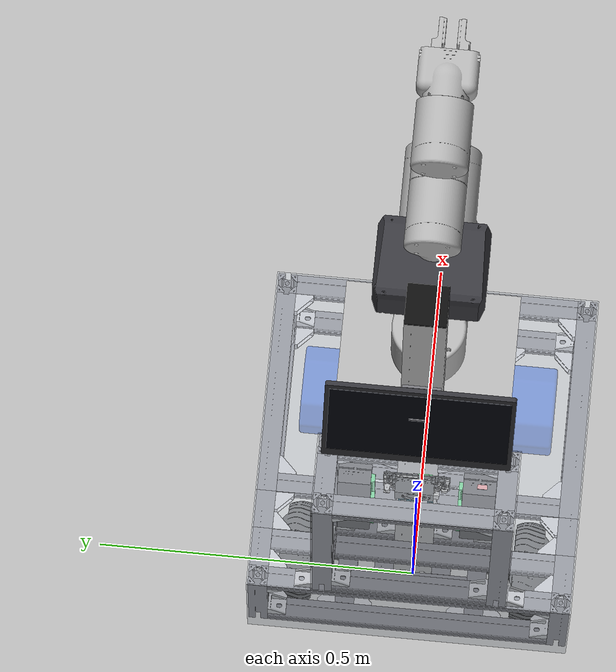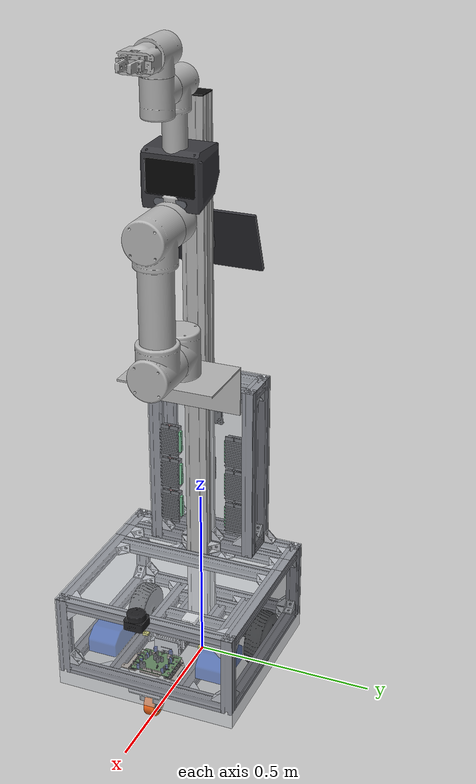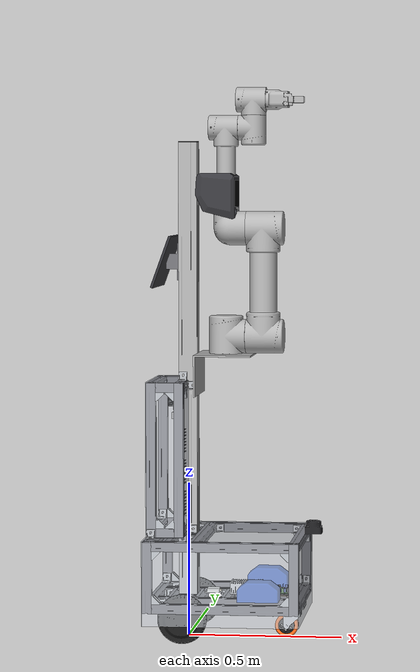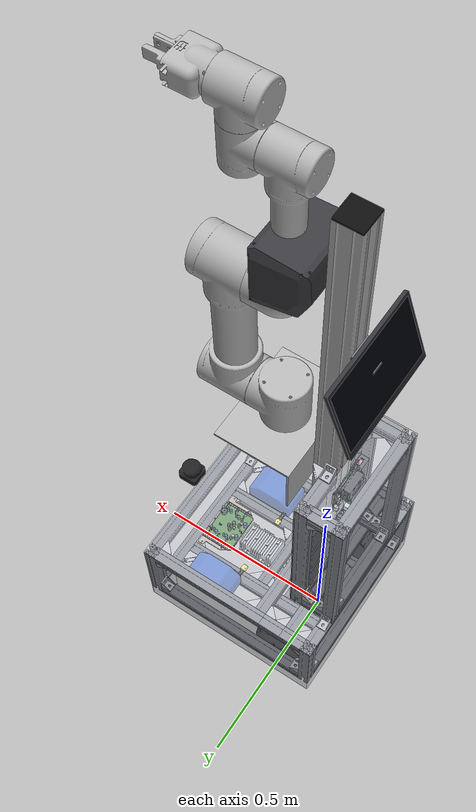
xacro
<?xml version="1.0" ?>
<robot name="andesrobot" xmlns:xacro="http://www.ros.org/wiki/xacro">

<!-- Colores (materials) y propiedades físicas para Gazebo (fricción de ruedas). -->
<xacro:include filename="$(find andesrobot_description)/urdf/andesrobot.materials.xacro" />
<xacro:include filename="$(find andesrobot_description)/urdf/andesrobot.gazebo.xacro" />

<xacro:arg name="lock_arm" default="false"/>
<!-- Convertir el texto "true"/"false" del argumento en un verdadero/falso de Python. -->
<xacro:property name="lock_arm" value="${'$(arg lock_arm)' == 'true'}"/>
<!-- Tipo de articulación del brazo: fixed si lock_arm, si no continuous (gira) / prismatic (desliza). -->
<xacro:property name="arm_joint_type" value="${'fixed' if lock_arm else 'revolute'}"/>
<xacro:property name="prismatic_joint_type" value="${'fixed' if lock_arm else 'prismatic'}"/>

<xacro:arg name="simple_collision" default="false"/>
<xacro:property name="simple_collision" value="${'$(arg simple_collision)' == 'true'}"/>
<xacro:arg name="arm_control" default="false"/>
<xacro:property name="arm_control" value="${'$(arg arm_control)' == 'true'}"/>
<xacro:arg name="arm_controllers_file" default=""/>
<!-- Interruptores de sensores simulados (para depurar). Los usa andesrobot.sim.xacro. -->
<xacro:arg name="sim_lidar" default="true"/>
<xacro:arg name="sim_imu" default="true"/>
  <!-- IMU de la pinza (andesrobot.gripper_imu.xacro) -->
  <material name="imu_blue">
    <color rgba="0.100 0.300 0.800 1.000"/>
  </material>
  <!-- Ruedas motrices: alta fricción -->
  <!-- Rueda loca: sin fricción (gira libre) -->
  <!-- masa total de estos links: 22.83 kg -->
  <material name="tapa_negra">
    <color rgba="0.05 0.05 0.05 1.0"/>
  </material>
  <link name="base_footprint"/>
  <joint name="base_footprint_joint" type="fixed">
    <!-- base_link = centro del eje de las ruedas motrices (centro de rotación del diff drive), a la altura del radio de rueda -->
    <origin rpy="0 0 0" xyz="0 0 0.08935"/>
    <!-- 0.08255 (radio de rueda) + 0.0068: con los SK16 el eje queda 6.8 mm bajo el origen de base_link -->
    <parent link="base_footprint"/>
    <child link="base_link"/>
  </joint>
  <!-- base_link: el CHASIS (bastidor de aluminio). Su origen está en el centro del eje de ruedas.
     Explico cada parte una vez aquí; los demás links tienen la misma estructura. -->
  <link name="base_link">
    <inertial>
      <origin rpy="0 0 0" xyz="0.1026 0.0000 0.1278"/>
      <mass value="5.8118"/>
      <inertia ixx="0.222355" ixy="0" ixz="0.00697789" iyy="0.231749" iyz="0" izz="0.346352"/>
    </inertial>
    <!-- Cómo se ve: la malla del CAD, corrida a su lugar (origin) y escalada de mm a m. -->
    <visual>  <!-- anillo inferior, lateral -->
      <origin rpy="0 1.5707963267948966 0" xyz="0.1300 -0.2350 0.035248"/>
      <geometry><mesh filename="file://$(find andesrobot_description)/meshes/vslot_3030_1m.stl" scale="0.001 0.001 0.000440"/></geometry>
      <material name="perfil_30x30"/>
    </visual>
    <visual>  <!-- anillo inferior, lateral -->
      <origin rpy="0 1.5707963267948966 0" xyz="0.1300 0.2350 0.035248"/>
      <geometry><mesh filename="file://$(find andesrobot_description)/meshes/vslot_3030_1m.stl" scale="0.001 0.001 0.000440"/></geometry>
      <material name="perfil_30x30"/>
    </visual>
    <visual>  <!-- anillo inferior, trasero -->
      <origin rpy="1.5707963267948966 0 0" xyz="-0.1050 0.0000 0.035248"/>
      <geometry><mesh filename="file://$(find andesrobot_description)/meshes/vslot_3030_1m.stl" scale="0.001 0.001 0.000440"/></geometry>
      <material name="perfil_30x30"/>
    </visual>
    <visual>  <!-- anillo inferior, delantero -->
      <origin rpy="1.5707963267948966 0 0" xyz="0.3650 0.0000 0.035248"/>
      <geometry><mesh filename="file://$(find andesrobot_description)/meshes/vslot_3030_1m.stl" scale="0.001 0.001 0.000440"/></geometry>
      <material name="perfil_30x30"/>
    </visual>
    <visual>  <!-- anillo superior, lateral -->
      <origin rpy="0 1.5707963267948966 0" xyz="0.1300 -0.2350 0.235248"/>
      <geometry><mesh filename="file://$(find andesrobot_description)/meshes/vslot_3030_1m.stl" scale="0.001 0.001 0.000440"/></geometry>
      <material name="perfil_30x30"/>
    </visual>
    <visual>  <!-- anillo superior, lateral -->
      <origin rpy="0 1.5707963267948966 0" xyz="0.1300 0.2350 0.235248"/>
      <geometry><mesh filename="file://$(find andesrobot_description)/meshes/vslot_3030_1m.stl" scale="0.001 0.001 0.000440"/></geometry>
      <material name="perfil_30x30"/>
    </visual>
    <visual>  <!-- anillo superior, trasero -->
      <origin rpy="1.5707963267948966 0 0" xyz="-0.1050 0.0000 0.235248"/>
      <geometry><mesh filename="file://$(find andesrobot_description)/meshes/vslot_3030_1m.stl" scale="0.001 0.001 0.000440"/></geometry>
      <material name="perfil_30x30"/>
    </visual>
    <visual>  <!-- anillo superior, delantero -->
      <origin rpy="1.5707963267948966 0 0" xyz="0.3650 0.0000 0.235248"/>
      <geometry><mesh filename="file://$(find andesrobot_description)/meshes/vslot_3030_1m.stl" scale="0.001 0.001 0.000440"/></geometry>
      <material name="perfil_30x30"/>
    </visual>
    <visual>  <!-- vertical esquina -->
      <origin rpy="0 0 0" xyz="-0.1050 -0.2350 0.135248"/>
      <geometry><mesh filename="file://$(find andesrobot_description)/meshes/vslot_3030_1m.stl" scale="0.001 0.001 0.000230"/></geometry>
      <material name="perfil_30x30"/>
    </visual>
    <visual>  <!-- vertical esquina -->
      <origin rpy="0 0 0" xyz="-0.1050 0.2350 0.135248"/>
      <geometry><mesh filename="file://$(find andesrobot_description)/meshes/vslot_3030_1m.stl" scale="0.001 0.001 0.000230"/></geometry>
      <material name="perfil_30x30"/>
    </visual>
    <visual>  <!-- vertical esquina -->
      <origin rpy="0 0 0" xyz="0.3650 -0.2350 0.135248"/>
      <geometry><mesh filename="file://$(find andesrobot_description)/meshes/vslot_3030_1m.stl" scale="0.001 0.001 0.000230"/></geometry>
      <material name="perfil_30x30"/>
    </visual>
    <visual>  <!-- vertical esquina -->
      <origin rpy="0 0 0" xyz="0.3650 0.2350 0.135248"/>
      <geometry><mesh filename="file://$(find andesrobot_description)/meshes/vslot_3030_1m.stl" scale="0.001 0.001 0.000230"/></geometry>
      <material name="perfil_30x30"/>
    </visual>
    <visual>  <!-- travesaño inferior largo -->
      <origin rpy="0 1.5707963267948966 0" xyz="0.1300 -0.1017 0.035248"/>
      <geometry><mesh filename="file://$(find andesrobot_description)/meshes/vslot_3030_1m.stl" scale="0.001 0.001 0.000440"/></geometry>
      <material name="perfil_30x30"/>
    </visual>
    <visual>  <!-- travesaño inferior largo -->
      <origin rpy="0 1.5707963267948966 0" xyz="0.1300 0.1017 0.035248"/>
      <geometry><mesh filename="file://$(find andesrobot_description)/meshes/vslot_3030_1m.stl" scale="0.001 0.001 0.000440"/></geometry>
      <material name="perfil_30x30"/>
    </visual>
    <visual>  <!-- travesaño inferior corto -->
      <origin rpy="1.5707963267948966 0 0" xyz="0.1300 0.0000 0.035248"/>
      <geometry><mesh filename="file://$(find andesrobot_description)/meshes/vslot_3030_1m.stl" scale="0.001 0.001 0.0001734"/></geometry>
      <material name="perfil_30x30"/>
    </visual>
    <visual>  <!-- travesaño inferior corto -->
      <origin rpy="1.5707963267948966 0 0" xyz="-0.0450 0.0000 0.035248"/>
      <geometry><mesh filename="file://$(find andesrobot_description)/meshes/vslot_3030_1m.stl" scale="0.001 0.001 0.0001734"/></geometry>
      <material name="perfil_30x30"/>
    </visual>
    <visual>  <!-- refuerzo columna, nivel inferior: travesaño delantero (cara frontal del 6060) -->
      <origin rpy="1.5707963267948966 0 0" xyz="0.0450 0.0000 0.035248"/>
      <geometry><mesh filename="file://$(find andesrobot_description)/meshes/vslot_3030_1m.stl" scale="0.001 0.001 0.0001734"/></geometry>
      <material name="perfil_30x30"/>
    </visual>
    <visual>  <!-- refuerzo columna, nivel inferior: tope lateral izq del 6060 -->
      <origin rpy="0 1.5707963267948966 0" xyz="0.0000 0.0450 0.035248"/>
      <geometry><mesh filename="file://$(find andesrobot_description)/meshes/vslot_3030_1m.stl" scale="0.001 0.001 0.0000600"/></geometry>
      <material name="perfil_30x30"/>
    </visual>
    <visual>  <!-- refuerzo columna, nivel inferior: tope lateral der del 6060 -->
      <origin rpy="0 1.5707963267948966 0" xyz="0.0000 -0.0450 0.035248"/>
      <geometry><mesh filename="file://$(find andesrobot_description)/meshes/vslot_3030_1m.stl" scale="0.001 0.001 0.0000600"/></geometry>
      <material name="perfil_30x30"/>
    </visual>
    <visual>  <!-- refuerzo columna, nivel superior: travesaño trasero de lado a lado (cara trasera del 6060) -->
      <origin rpy="1.5707963267948966 0 0" xyz="-0.0450 0.0000 0.235248"/>
      <geometry><mesh filename="file://$(find andesrobot_description)/meshes/vslot_3030_1m.stl" scale="0.001 0.001 0.0004400"/></geometry>
      <material name="perfil_30x30"/>
    </visual>
    <visual>  <!-- refuerzo columna, nivel superior: travesaño delantero de lado a lado (cara frontal del 6060) -->
      <origin rpy="1.5707963267948966 0 0" xyz="0.0450 0.0000 0.235248"/>
      <geometry><mesh filename="file://$(find andesrobot_description)/meshes/vslot_3030_1m.stl" scale="0.001 0.001 0.0004400"/></geometry>
      <material name="perfil_30x30"/>
    </visual>
    <visual>  <!-- refuerzo columna, nivel superior: tope lateral izq del 6060 -->
      <origin rpy="0 1.5707963267948966 0" xyz="0.0000 0.0450 0.235248"/>
      <geometry><mesh filename="file://$(find andesrobot_description)/meshes/vslot_3030_1m.stl" scale="0.001 0.001 0.0000600"/></geometry>
      <material name="perfil_30x30"/>
    </visual>
    <visual>  <!-- refuerzo columna, nivel superior: tope lateral der del 6060 -->
      <origin rpy="0 1.5707963267948966 0" xyz="0.0000 -0.0450 0.235248"/>
      <geometry><mesh filename="file://$(find andesrobot_description)/meshes/vslot_3030_1m.stl" scale="0.001 0.001 0.0000600"/></geometry>
      <material name="perfil_30x30"/>
    </visual>
    <collision name="chasis">
      <origin rpy="0 0 0" xyz="0.13 0 0.115"/>
      <geometry>
        <box size="0.50 0.50 0.27"/>
      </geometry>
    </collision>
    <collision name="columna">
      <origin rpy="0 0 0" xyz="0 0 0.77"/>
      <geometry>
        <box size="0.06 0.06 1.50"/>
      </geometry>
    </collision>
    <collision name="rplidar_c1">
      <origin rpy="0 0 0" xyz="0.408 0 0.271"/>
      <geometry>
        <cylinder length="0.042" radius="0.028"/>
      </geometry>
    </collision>
    <!-- simple_collision:=true (pensado con lock_arm:=true): el carro y el brazo PLEGADO chocan como dos cajas
         pegadas al chasis (medidas de las mallas en la pose plegada, frame base_link). -->
    <xacro:if value="${simple_collision}">
    <collision name="carro_lift">
      <origin rpy="0 0 0" xyz="0.1225 0 0.3702"/>
      <geometry>
        <box size="0.185 0.26 0.135"/>
      </geometry>
    </collision>
    <collision name="brazo_plegado">
      <origin rpy="0 0 0" xyz="0.1985 -0.0075 0.6382"/>
      <geometry>
        <box size="0.343 0.465 0.401"/>
      </geometry>
    </collision>
    </xacro:if>
  </link>
  <!-- Brazo, eslabón 1: base giratoria del brazo (gira en Z sobre arm_base_link_1). -->
  <link name="link_1_1">
    <inertial>
      <!-- Pieza impresa en PLA (1.24 g/cm³): 4 paredes (1.6 mm), 7 capas techo/piso (1.4 mm), relleno 60 %.
           Masa, centro de masa e inercia calculados de la malla por voxeles de 0.5 mm (408.9 cm³). -->
      <origin rpy="0 0 0" xyz="-0.01311 0.00001 0.06439"/>
      <mass value="0.3801"/>
      <inertia ixx="9.9601e-04" ixy="-9.2665e-08" ixz="-4.3879e-05" iyy="1.0780e-03" iyz="2.1490e-07" izz="1.0451e-03"/>
    </inertial>
    <visual>
      <origin rpy="0 0 0" xyz="-0.0075 -0.0 -0.3545"/>
      <geometry>
        <mesh filename="file://$(find andesrobot_description)/meshes/link_1_1.stl" scale="0.001 0.001 0.001"/>
      </geometry>
      <material name="silver"/>
    </visual>
    <!-- Colisión con la malla CAD: solo si simple_collision es falso. -->
    <xacro:unless value="${simple_collision}">
    <collision>
      <origin rpy="0 0 0" xyz="-0.0075 -0.0 -0.3545"/>
      <geometry>
        <mesh filename="file://$(find andesrobot_description)/meshes/link_1_1.stl" scale="0.001 0.001 0.001"/>
      </geometry>
    </collision>
    </xacro:unless>
  </link>
  <!-- Brazo, eslabón 2: hombro. -->
  <link name="link_2_1">
    <inertial>
      <!-- Pieza impresa en PLA (1.24 g/cm³): 4 paredes (1.6 mm), 7 capas techo/piso (1.4 mm), relleno 60 %.
           Masa, centro de masa e inercia calculados de la malla por voxeles de 0.5 mm (1261.5 cm³). -->
      <origin rpy="0 0 0" xyz="-0.06166 0.00004 0.17377"/>
      <mass value="1.1570"/>
      <inertia ixx="2.3695e-02" ixy="-9.4959e-08" ixz="7.7567e-05" iyy="2.3760e-02" iyz="5.7097e-06" izz="2.7043e-03"/>
    </inertial>
    <visual>
      <origin rpy="0 0 0" xyz="0.0575 -0.0 -0.4105"/>
      <geometry>
        <mesh filename="file://$(find andesrobot_description)/meshes/link_2_1.stl" scale="0.001 0.001 0.001"/>
      </geometry>
      <material name="silver"/>
    </visual>
    <!-- Colisión con la malla CAD: solo si simple_collision es falso. -->
    <xacro:unless value="${simple_collision}">
    <collision>
      <origin rpy="0 0 0" xyz="0.0575 -0.0 -0.4105"/>
      <geometry>
        <mesh filename="file://$(find andesrobot_description)/meshes/link_2_1.stl" scale="0.001 0.001 0.001"/>
      </geometry>
    </collision>
    </xacro:unless>
  </link>
  <!-- Brazo, eslabón 3: codo. -->
  <link name="link_3_1">
    <inertial>
      <!-- Pieza impresa en PLA (1.24 g/cm³): 4 paredes (1.6 mm), 7 capas techo/piso (1.4 mm), relleno 60 %.
           Masa, centro de masa e inercia calculados de la malla por voxeles de 0.5 mm (712.4 cm³). -->
      <origin rpy="0 0 0" xyz="0.06132 -0.00001 0.14817"/>
      <mass value="0.6736"/>
      <inertia ixx="1.2451e-02" ixy="9.5805e-08" ixz="-1.1313e-03" iyy="1.2621e-02" iyz="4.4111e-07" izz="1.1167e-03"/>
    </inertial>
    <visual>
      <origin rpy="0 0 0" xyz="0.058577 -0.0 -0.760577"/>
      <geometry>
        <mesh filename="file://$(find andesrobot_description)/meshes/link_3_1.stl" scale="0.001 0.001 0.001"/>
      </geometry>
      <material name="silver"/>
    </visual>
    <!-- Colisión con la malla CAD: solo si simple_collision es falso. -->
    <xacro:unless value="${simple_collision}">
    <collision>
      <origin rpy="0 0 0" xyz="0.058577 -0.0 -0.760577"/>
      <geometry>
        <mesh filename="file://$(find andesrobot_description)/meshes/link_3_1.stl" scale="0.001 0.001 0.001"/>
      </geometry>
    </collision>
    </xacro:unless>
  </link>
  <!-- Brazo, eslabón 4: muñeca (inclinación). -->
  <link name="link_4_1">
    <inertial>
      <!-- Pieza impresa en PLA (1.24 g/cm³): 4 paredes (1.6 mm), 7 capas techo/piso (1.4 mm), relleno 60 %.
           Masa, centro de masa e inercia calculados de la malla por voxeles de 0.5 mm (210.1 cm³). -->
      <origin rpy="0 0 0" xyz="-0.04027 -0.00001 -0.01026"/>
      <mass value="0.1972"/>
      <inertia ixx="2.8668e-04" ixy="-1.8992e-08" ixz="-1.9064e-05" iyy="3.1663e-04" iyz="-6.6382e-08" izz="2.8419e-04"/>
    </inertial>
    <visual>
      <origin rpy="0 0 0" xyz="0.032577 -0.0 -1.084077"/>
      <geometry>
        <mesh filename="file://$(find andesrobot_description)/meshes/link_4_1.stl" scale="0.001 0.001 0.001"/>
      </geometry>
      <material name="silver"/>
    </visual>
    <!-- Colisión con la malla CAD: solo si simple_collision es falso. -->
    <xacro:unless value="${simple_collision}">
    <collision>
      <origin rpy="0 0 0" xyz="0.032577 -0.0 -1.084077"/>
      <geometry>
        <mesh filename="file://$(find andesrobot_description)/meshes/link_4_1.stl" scale="0.001 0.001 0.001"/>
      </geometry>
    </collision>
    </xacro:unless>
  </link>
  <!-- Brazo, eslabón 5: muñeca (giro). -->
  <link name="link_5_1">
    <inertial>
      <!-- Pieza impresa en PLA (1.24 g/cm³): 4 paredes (1.6 mm), 7 capas techo/piso (1.4 mm), relleno 60 %.
           Masa, centro de masa e inercia calculados de la malla por voxeles de 0.5 mm (212.3 cm³). -->
      <origin rpy="0 0 0" xyz="0.00958 -0.00001 0.04022"/>
      <mass value="0.1964"/>
      <inertia ixx="2.8107e-04" ixy="5.8276e-08" ixz="-1.7814e-05" iyy="3.2051e-04" iyz="2.0678e-08" izz="2.9288e-04"/>
    </inertial>
    <visual>
      <origin rpy="0 0 0" xyz="0.082077 -0.0 -1.124077"/>
      <geometry>
        <mesh filename="file://$(find andesrobot_description)/meshes/link_5_1.stl" scale="0.001 0.001 0.001"/>
      </geometry>
      <material name="silver"/>
    </visual>
    <!-- Colisión con la malla CAD: solo si simple_collision es falso. -->
    <xacro:unless value="${simple_collision}">
    <collision>
      <origin rpy="0 0 0" xyz="0.082077 -0.0 -1.124077"/>
      <geometry>
        <mesh filename="file://$(find andesrobot_description)/meshes/link_5_1.stl" scale="0.001 0.001 0.001"/>
      </geometry>
    </collision>
    </xacro:unless>
  </link>
  <!-- Brazo, eslabón 6: muñeca final, donde va la pinza. -->
  <link name="link_6_1">
    <inertial>
      <!-- Pieza impresa en PLA (1.24 g/cm³): 4 paredes (1.6 mm), 7 capas techo/piso (1.4 mm), relleno 60 %.
           Masa, centro de masa e inercia calculados de la malla por voxeles de 0.5 mm (94.1 cm³). -->
      <origin rpy="0 0 0" xyz="-0.04402 0.00054 -0.00013"/>
      <mass value="0.0936"/>
      <inertia ixx="9.5872e-05" ixy="3.6959e-07" ixz="-2.1542e-07" iyy="6.9804e-05" iyz="-5.8304e-08" izz="1.0245e-04"/>
    </inertial>
    <visual>
      <origin rpy="0 0 0" xyz="0.123077 -0.0 -1.173577"/>
      <geometry>
        <mesh filename="file://$(find andesrobot_description)/meshes/link_6_1.stl" scale="0.001 0.001 0.001"/>
      </geometry>
      <material name="silver"/>
    </visual>
    <!-- Colisión con la malla CAD: solo si simple_collision es falso. -->
    <xacro:unless value="${simple_collision}">
    <collision>
      <origin rpy="0 0 0" xyz="0.123077 -0.0 -1.173577"/>
      <geometry>
        <mesh filename="file://$(find andesrobot_description)/meshes/link_6_1.stl" scale="0.001 0.001 0.001"/>
      </geometry>
    </collision>
    </xacro:unless>
  </link>
  <!-- Pinza: dedo derecho. -->
  <link name="right_finger_link_1">
    <inertial>
      <!-- Pieza impresa en PLA (1.24 g/cm³): 4 paredes (1.6 mm), 7 capas techo/piso (1.4 mm), relleno 60 %.
           Masa, centro de masa e inercia calculados de la malla por voxeles de 0.5 mm (21.1 cm³). -->
      <origin rpy="0 0 0" xyz="-0.02416 0.01348 -0.00710"/>
      <mass value="0.0201"/>
      <inertia ixx="5.4433e-06" ixy="1.9808e-06" ixz="-1.9680e-06" iyy="8.3687e-06" iyz="1.0427e-06" izz="1.0569e-05"/>
    </inertial>
    <visual>
      <origin rpy="0 0 0" xyz="0.180677 0.0038 -1.187077"/>
      <geometry>
        <mesh filename="file://$(find andesrobot_description)/meshes/right_finger_link_1.stl" scale="0.001 0.001 0.001"/>
      </geometry>
      <material name="silver"/>
    </visual>
    <!-- Colisión con la malla CAD: solo si simple_collision es falso. -->
    <xacro:unless value="${simple_collision}">
    <collision>
      <origin rpy="0 0 0" xyz="0.180677 0.0038 -1.187077"/>
      <geometry>
        <mesh filename="file://$(find andesrobot_description)/meshes/right_finger_link_1.stl" scale="0.001 0.001 0.001"/>
      </geometry>
    </collision>
    </xacro:unless>
  </link>
  <!-- Pinza: dedo izquierdo. -->
  <link name="left_finger_link_1">
    <inertial>
      <!-- Pieza impresa en PLA (1.24 g/cm³): 4 paredes (1.6 mm), 7 capas techo/piso (1.4 mm), relleno 60 %.
           Masa, centro de masa e inercia calculados de la malla por voxeles de 0.5 mm (21.1 cm³). -->
      <origin rpy="0 0 0" xyz="-0.02426 -0.01324 0.00738"/>
      <mass value="0.0201"/>
      <inertia ixx="5.4246e-06" ixy="-1.9524e-06" ixz="1.9472e-06" iyy="8.3276e-06" iyz="1.0288e-06" izz="1.0539e-05"/>
    </inertial>
    <visual>
      <origin rpy="0 0 0" xyz="0.180677 -0.0038 -1.160077"/>
      <geometry>
        <mesh filename="file://$(find andesrobot_description)/meshes/left_finger_link_1.stl" scale="0.001 0.001 0.001"/>
      </geometry>
      <material name="silver"/>
    </visual>
    <!-- Colisión con la malla CAD: solo si simple_collision es falso. -->
    <xacro:unless value="${simple_collision}">
    <collision>
      <origin rpy="0 0 0" xyz="0.180677 -0.0038 -1.160077"/>
      <geometry>
        <mesh filename="file://$(find andesrobot_description)/meshes/left_finger_link_1.stl" scale="0.001 0.001 0.001"/>
      </geometry>
    </collision>
    </xacro:unless>
  </link>
  <!-- Carro del elevador: sube y baja por la columna llevando el brazo. -->
  <link name="lift_carriage_link_1">
    <inertial>
      <origin rpy="0 0 0" xyz="-0.0553571 0 0.0371429"/>
      <mass value="0.8"/>
      <inertia ixx="0.00585609" ixy="0" ixz="0.00117796" iyy="0.00426075" iyz="0" izz="0.00741799"/>
    </inertial>
    <visual>
      <origin rpy="0 0 0" xyz="-0.1 -0.0 -0.25"/>
      <geometry>
        <mesh filename="file://$(find andesrobot_description)/meshes/lift_carriage_link_1.stl" scale="0.001 0.001 0.001"/>
      </geometry>
      <material name="silver"/>
    </visual>
    <!-- Colisión con la malla CAD: solo si simple_collision es falso. -->
    <xacro:unless value="${simple_collision}">
    <collision>
      <origin rpy="0 0 0" xyz="-0.1 -0.0 -0.25"/>
      <geometry>
        <mesh filename="file://$(find andesrobot_description)/meshes/lift_carriage_link_1.stl" scale="0.001 0.001 0.001"/>
      </geometry>
    </collision>
    </xacro:unless>
  </link>
  <!-- Rueda motriz izquierda (rueda de hoverboard 6.5", radio 0.08255 m). -->
  <material name="rueda_negra">
    <color rgba="0.10 0.10 0.10 1.0"/>
  </material>
  <link name="left_wheel_link_1">
    <!-- Motor rueda hoverboard 6.5" 350 W: ~3 kg (repuesto 36 V 350 W listado en 3 kg; el Parallax de 6.5" pesa 3.6 kg) -->
    <inertial>
      <origin rpy="0 0 0" xyz="1.69549e-10 -0.0224998 8.55927e-08"/>
      <mass value="3.0000"/>
      <inertia ixx="0.00618025" ixy="0" ixz="0" iyy="0.011348" iyz="0" izz="0.00618025"/>
    </inertial>
    <visual>
      <!-- Motor rueda hoverboard 6.5" (GrabCAD, John Frank). Ø158.8 mm, eje hacia adentro del robot. -->
      <origin rpy="0 0 -1.5707963267948966" xyz="0 0.006 0"/>
      <geometry>
        <mesh filename="file://$(find andesrobot_description)/meshes/rueda_hoverboard_6_5.stl" scale="0.001 0.001 0.001"/>
      </geometry>
      <material name="rueda_negra"/>
    </visual>
    <collision>
      <!-- cilindro ideal: r=0.08255, ancho 0.045 (medido de la malla) -->
      <!-- rpy 1.5708 (90°) en x acuesta el cilindro para que su eje quede a lo ancho, como una rueda. -->
      <origin rpy="1.5707963267948966 0 0" xyz="0 -0.0225 0"/>
      <geometry>
        <cylinder length="0.045" radius="0.08255"/>
      </geometry>
    </collision>
  </link>
  <!-- Rueda motriz derecha. -->
  <link name="right_wheel_link_1">
    <!-- Motor rueda hoverboard 6.5" 350 W: ~3 kg (repuesto 36 V 350 W listado en 3 kg; el Parallax de 6.5" pesa 3.6 kg) -->
    <inertial>
      <origin rpy="0 0 0" xyz="1.69549e-10 0.0224998 -2.02646e-09"/>
      <mass value="3.0000"/>
      <inertia ixx="0.00618025" ixy="0" ixz="0" iyy="0.011348" iyz="0" izz="0.00618025"/>
    </inertial>
    <visual>
      <!-- Motor rueda hoverboard 6.5" (GrabCAD, John Frank). Ø158.8 mm, eje hacia adentro del robot. -->
      <origin rpy="0 0 1.5707963267948966" xyz="0 -0.006 0"/>
      <geometry>
        <mesh filename="file://$(find andesrobot_description)/meshes/rueda_hoverboard_6_5.stl" scale="0.001 0.001 0.001"/>
      </geometry>
      <material name="rueda_negra"/>
    </visual>
    <collision>
      <!-- cilindro ideal: r=0.08255, ancho 0.045 (medido de la malla) -->
      <origin rpy="1.5707963267948966 0 0" xyz="0 0.0225 0"/>
      <geometry>
        <cylinder length="0.045" radius="0.08255"/>
      </geometry>
    </collision>
  </link>
  <!-- IMU (acelerómetro + giroscopio). -->
  <material name="imu_blanco">
    <color rgba="0.93 0.93 0.92 1.0"/>
  </material>
  <material name="imu_conector">
    <color rgba="0.95 0.90 0.78 1.0"/>
  </material>
  <link name="imu_link_1">
    <inertial>
      <origin rpy="0 0 0" xyz="0 0 0.007"/>
      <mass value="0.02"/>
      <inertia ixx="2.993e-06" ixy="0" ixz="0" iyy="2.993e-06" iyz="0" izz="5.333e-06"/>
    </inertial>
    <visual>
      <origin rpy="0 0 0" xyz="0 0 0"/>
      <geometry><mesh filename="file://$(find andesrobot_description)/meshes/imu_hfi_b9_cuerpo.stl" scale="0.001 0.001 0.001"/></geometry>
      <material name="imu_blanco"/>
    </visual>
    <visual>
      <origin rpy="0 0 0" xyz="0 0 0"/>
      <geometry><mesh filename="file://$(find andesrobot_description)/meshes/imu_hfi_b9_conector.stl" scale="0.001 0.001 0.001"/></geometry>
      <material name="imu_conector"/>
    </visual>
  </link>
  <material name="rueda_loca_acero">
    <color rgba="0.78 0.80 0.82 1.0"/>
  </material>
  <material name="rueda_loca_pu">
    <color rgba="1.0 0.42 0.10 1.0"/>
  </material>
  <material name="rueda_loca_nucleo">
    <color rgba="0.10 0.10 0.10 1.0"/>
  </material>
  <link name="front_caster_link_1">
    <!-- Rueda 3" con freno ~0.40 kg (similares de 75 mm con freno: 0.34 kg) + suplencia de aluminio 62x93x9.6 mm 0.149 kg -->
    <inertial>
      <origin rpy="0 0 0" xyz="0.015 0 -0.045"/>
      <mass value="0.5490"/>
      <inertia ixx="0.000549" ixy="0" ixz="0" iyy="0.00061" iyz="0" izz="0.000366"/>
    </inertial>
    <!-- suplencia de aluminio de 9.6 mm entre el bastidor y la placa (el bastidor queda a 109.6 mm del suelo) -->
    <visual>
      <origin rpy="0 0 0" xyz="0 0 0.0048"/>
      <geometry>
        <box size="0.062 0.093 0.0096"/>
      </geometry>
      <material name="aluminio_herraje"/>
    </visual>
    <visual>
      <origin rpy="0 0 0" xyz="0 0 0"/>
      <geometry><mesh filename="file://$(find andesrobot_description)/meshes/rueda_loca_acero.stl" scale="0.001 0.001 0.001"/></geometry>
      <material name="rueda_loca_acero"/>
    </visual>
    <visual>
      <origin rpy="0 0 0" xyz="0 0 0"/>
      <geometry><mesh filename="file://$(find andesrobot_description)/meshes/rueda_loca_pu.stl" scale="0.001 0.001 0.001"/></geometry>
      <material name="rueda_loca_pu"/>
    </visual>
    <visual>
      <origin rpy="0 0 0" xyz="0 0 0"/>
      <geometry><mesh filename="file://$(find andesrobot_description)/meshes/rueda_loca_nucleo.stl" scale="0.001 0.001 0.001"/></geometry>
      <material name="rueda_loca_nucleo"/>
    </visual>
    <!-- colisión: esfera sin fricción del tamaño de la rueda (aprox. estándar de rueda loca en Gazebo) -->
    <collision>
      <origin rpy="0 0 0" xyz="0.028 0 -0.0625"/>
      <geometry>
        <sphere radius="0.0375"/>
      </geometry>
    </collision>
  </link>
  <!-- Carcasa del RPLIDAR C1. El frame exacto de medición es "laser" (más abajo). -->
  <link name="lidar_link_1">
    <inertial>
      <origin rpy="0 0 0" xyz="-0.058 0 0.0227"/>
      <mass value="0.11"/>
      <inertia ixx="4.4e-05" ixy="0.0" ixz="0.0" iyy="4.4e-05" iyz="0.0" izz="5.7e-05"/>
    </inertial>
    <visual>
      <origin rpy="0 0 3.141592653589793" xyz="-0.058 0 0.002"/>
      <geometry>
        <mesh filename="file://$(find andesrobot_description)/meshes/rplidar_c1.stl" scale="0.001 0.001 0.001"/>
      </geometry>
      <material name="lidar_negro"/>
    </visual>
  </link>
  <material name="lidar_negro">
    <color rgba="0.12 0.12 0.13 1.0"/>
  </material>
  <!-- Columna vertical (perfil de 1.5 m) por donde sube el carro del elevador. -->
  <link name="vertical_column_link_1">
    <inertial>
      <origin rpy="0 0 0" xyz="-0.03 0 0.75"/>
      <mass value="3.9"/>
      <inertia ixx="0.73242" ixy="0" ixz="0" iyy="0.73242" iyz="0" izz="0.00234"/>
    </inertial>
    <visual>
      <!-- Perfil V-slot 6060 de 1.5 m (malla de 1 m estirada en z; la sección no cambia) -->
      <origin rpy="0 0 0" xyz="-0.03 0 0.75"/>
      <geometry>
        <mesh filename="file://$(find andesrobot_description)/meshes/vslot_6060_1m.stl" scale="0.001 0.001 0.0015"/>
      </geometry>
      <material name="silver"/>
    </visual>
    <!-- Tapa plástica del extremo superior del 6060 (4 mm, con tetón que entra al hueco central) -->
    <visual>
      <origin rpy="0 0 0" xyz="-0.03 0 1.5"/>
      <geometry>
        <mesh filename="file://$(find andesrobot_description)/meshes/tapa_6060.stl" scale="0.001 0.001 0.001"/>
      </geometry>
      <material name="tapa_negra"/>
    </visual>
  </link>
  <link name="arm_base_link_1"/>
  <xacro:property name="arm_lower" value="${-pi}"/>
  <xacro:property name="arm_upper" value="${pi}"/>
  <xacro:property name="arm_effort" value="20.0"/>
  <xacro:property name="arm_velocity" value="1.0"/>
  <xacro:property name="joint_1_lower" value="${arm_lower}"/>   <!-- [rad] provisorio -->
  <xacro:property name="joint_1_upper" value="${arm_upper}"/>
  <xacro:property name="joint_2_lower" value="${arm_lower}"/>
  <xacro:property name="joint_2_upper" value="${arm_upper}"/>
  <xacro:property name="joint_3_lower" value="${arm_lower}"/>
  <xacro:property name="joint_3_upper" value="${arm_upper}"/>
  <xacro:property name="joint_4_lower" value="${arm_lower}"/>
  <xacro:property name="joint_4_upper" value="${arm_upper}"/>
  <xacro:property name="joint_5_lower" value="${arm_lower}"/>
  <xacro:property name="joint_5_upper" value="${arm_upper}"/>
  <xacro:property name="joint_6_lower" value="${arm_lower}"/>
  <xacro:property name="joint_6_upper" value="${arm_upper}"/>
  <!-- Límite de cada articulación del brazo (las "fixed" no llevan límite). -->
  <xacro:macro name="arm_limit" params="lower upper">
    <xacro:unless value="${lock_arm}">
      <limit lower="${lower}" upper="${upper}" effort="${arm_effort}" velocity="${arm_velocity}"/>
    </xacro:unless>
  </xacro:macro>
  <!-- Brazo 1: gira la base del brazo alrededor de Z (vertical). -->
  <joint name="joint_1" type="${arm_joint_type}">
    <!-- Brazo directo sobre la placa del carro (antes 3.7 cm más arriba, sobre la base con nervios). -->
    <!-- lock_arm: pose plegada (rpy horneado); móvil: 0 = estirado. -->
    <origin rpy="${'0 0 0.2775' if lock_arm else '0 0 0'}" xyz="0.0 0.0 0.0"/>
    <parent link="arm_base_link_1"/>
    <child link="link_1_1"/>
    <!-- Eje de giro (0 0 1 = Z). -->
    <axis xyz="0.0 0.0 1.0"/>
    <!-- Amortiguación y roce de la articulación (solo para la simulación). -->
    <dynamics damping="0.08" friction="0.02"/>
    <xacro:arm_limit lower="${joint_1_lower}" upper="${joint_1_upper}"/>
  </joint>
  <!-- Brazo 2 (hombro): gira alrededor de X. -->
  <joint name="joint_2" type="${arm_joint_type}">
    <!-- lock_arm: pose plegada (rpy horneado); móvil: 0 = estirado. -->
    <origin rpy="${'-0.5965 0 0' if lock_arm else '0 0 0'}" xyz="-0.065 0.0 0.056"/>
    <parent link="link_1_1"/>
    <child link="link_2_1"/>
    <axis xyz="-1.0 0.0 0.0"/>
    <dynamics damping="0.12" friction="0.03"/>
    <xacro:arm_limit lower="${joint_2_lower}" upper="${joint_2_upper}"/>
  </joint>
  <!-- Brazo 3 (codo): gira alrededor de X. -->
  <joint name="joint_3" type="${arm_joint_type}">
    <!-- lock_arm: pose plegada (rpy horneado); móvil: 0 = estirado. -->
    <origin rpy="${'2.4000 0 0' if lock_arm else '0 0 0'}" xyz="-0.001077 0.0 0.350077"/>
    <parent link="link_2_1"/>
    <child link="link_3_1"/>
    <axis xyz="1.0 0.0 0.0"/>
    <dynamics damping="0.12" friction="0.03"/>
    <xacro:arm_limit lower="${joint_3_lower}" upper="${joint_3_upper}"/>
  </joint>
  <!-- Brazo 4 (muñeca): gira alrededor de X. -->
  <joint name="joint_4" type="${arm_joint_type}">
    <!-- lock_arm: pose plegada (rpy horneado); móvil: 0 = estirado. -->
    <origin rpy="${'1.0642 0 0' if lock_arm else '0 0 0'}" xyz="0.026 0.0 0.3235"/>
    <parent link="link_3_1"/>
    <child link="link_4_1"/>
    <axis xyz="-1.0 0.0 0.0"/>
    <dynamics damping="0.06" friction="0.02"/>
    <xacro:arm_limit lower="${joint_4_lower}" upper="${joint_4_upper}"/>
  </joint>
  <!-- Brazo 5 (muñeca): gira alrededor de Z. -->
  <joint name="joint_5" type="${arm_joint_type}">
    <!-- lock_arm: pose plegada (rpy horneado); móvil: 0 = estirado. -->
    <origin rpy="${'0 0 1.8334' if lock_arm else '0 0 0'}" xyz="-0.0495 0.0 0.04"/>
    <parent link="link_4_1"/>
    <child link="link_5_1"/>
    <axis xyz="0.0 0.0 1.0"/>
    <dynamics damping="0.05" friction="0.02"/>
    <xacro:arm_limit lower="${joint_5_lower}" upper="${joint_5_upper}"/>
  </joint>
  <!-- Brazo 6 (muñeca): gira alrededor de X. -->
  <joint name="joint_6" type="${arm_joint_type}">
    <!-- lock_arm: pose plegada (rpy horneado); móvil: 0 = estirado. -->
    <origin rpy="${'-0.8381 0 0' if lock_arm else '0 0 0'}" xyz="-0.041 0.0 0.0495"/>
    <parent link="link_5_1"/>
    <child link="link_6_1"/>
    <axis xyz="-1.0 0.0 0.0"/>
    <dynamics damping="0.05" friction="0.02"/>
    <xacro:arm_limit lower="${joint_6_lower}" upper="${joint_6_upper}"/>
  </joint>
  <link name="gripper_tcp"/>
  <joint name="gripper_tcp_joint" type="fixed">
    <origin xyz="-0.102 0.0 0.0" rpy="0 0 0"/>
    <parent link="link_6_1"/>
    <child link="gripper_tcp"/>
  </joint>
  <!-- rad (~10°) hacia los dedos -->
  <!-- NEMA23 1.26 N·m (tipo 23HS22-2804S), 57x57x56 mm, 0.70 kg -->
  <link name="motor_joint_1">
    <inertial>
      <origin rpy="0 0 0" xyz="0 0 0"/>
      <mass value="0.7"/>
      <inertia ixx="3.7246e-04" ixy="0" ixz="0" iyy="3.7246e-04" iyz="0" izz="3.7905e-04"/>
    </inertial>
  </link>
  <joint name="motor_joint_1_joint" type="fixed">
    <origin rpy="0 0 0" xyz="0.0 0.0 0.0"/>
    <parent link="arm_base_link_1"/>
    <child link="motor_joint_1"/>
  </joint>
  <!-- NEMA23 2.9 N·m (clase 3 N·m: 23HS45-4204S), 57x57x113 mm, 1.60 kg -->
  <link name="motor_joint_2">
    <inertial>
      <origin rpy="0 0 0" xyz="0 0 0"/>
      <mass value="1.6"/>
      <inertia ixx="8.6640e-04" ixy="0" ixz="0" iyy="2.1357e-03" iyz="0" izz="2.1357e-03"/>
    </inertial>
  </link>
  <joint name="motor_joint_2_joint" type="fixed">
    <origin rpy="0 0 0" xyz="-0.065 0.0 0.056"/>
    <parent link="link_1_1"/>
    <child link="motor_joint_2"/>
  </joint>
  <!-- NEMA23 1.26 N·m (tipo 23HS22-2804S), 57x57x56 mm, 0.70 kg -->
  <link name="motor_joint_3">
    <inertial>
      <origin rpy="0 0 0" xyz="0 0 0"/>
      <mass value="0.7"/>
      <inertia ixx="3.7905e-04" ixy="0" ixz="0" iyy="3.7246e-04" iyz="0" izz="3.7246e-04"/>
    </inertial>
  </link>
  <joint name="motor_joint_3_joint" type="fixed">
    <origin rpy="0 0 0" xyz="-0.001077 0.0 0.350077"/>
    <parent link="link_2_1"/>
    <child link="motor_joint_3"/>
  </joint>
  <!-- NEMA17 de Anet A8 (42SHDC3025-24B, ~0.45 N·m), 42x42x40 mm, ~0.28 kg -->
  <link name="motor_joint_4">
    <inertial>
      <origin rpy="0 0 0" xyz="0 0 0"/>
      <mass value="0.28"/>
      <inertia ixx="8.2320e-05" ixy="0" ixz="0" iyy="7.8493e-05" iyz="0" izz="7.8493e-05"/>
    </inertial>
  </link>
  <joint name="motor_joint_4_joint" type="fixed">
    <origin rpy="0 0 0" xyz="0.026 0.0 0.3235"/>
    <parent link="link_3_1"/>
    <child link="motor_joint_4"/>
  </joint>
  <!-- NEMA17 de Anet A8 (42SHDC3025-24B, ~0.45 N·m), 42x42x40 mm, ~0.28 kg -->
  <link name="motor_joint_5">
    <inertial>
      <origin rpy="0 0 0" xyz="0 0 0"/>
      <mass value="0.28"/>
      <inertia ixx="7.8493e-05" ixy="0" ixz="0" iyy="7.8493e-05" iyz="0" izz="8.2320e-05"/>
    </inertial>
  </link>
  <joint name="motor_joint_5_joint" type="fixed">
    <origin rpy="0 0 0" xyz="-0.0495 0.0 0.04"/>
    <parent link="link_4_1"/>
    <child link="motor_joint_5"/>
  </joint>
  <!-- NEMA17 de Anet A8 (42SHDC3025-24B, ~0.45 N·m), 42x42x40 mm, ~0.28 kg -->
  <link name="motor_joint_6">
    <inertial>
      <origin rpy="0 0 0" xyz="0 0 0"/>
      <mass value="0.28"/>
      <inertia ixx="8.2320e-05" ixy="0" ixz="0" iyy="7.8493e-05" iyz="0" izz="7.8493e-05"/>
    </inertial>
  </link>
  <joint name="motor_joint_6_joint" type="fixed">
    <origin rpy="0 0 0" xyz="-0.041 0.0 0.0495"/>
    <parent link="link_5_1"/>
    <child link="motor_joint_6"/>
  </joint>
  <!-- Servo de la pinza (MG996R, ~55 g), dentro del cuerpo de la pinza; caja 40 x 20 x 43 mm (como en milo_ws) -->
  <link name="gripper_servo_link">
    <inertial>
      <origin rpy="0 0 0" xyz="0 0 0"/>
      <mass value="0.055"/>
      <inertia ixx="1.0308e-05" ixy="0" ixz="0" iyy="1.5808e-05" iyz="0" izz="9.1667e-06"/>
    </inertial>
  </link>
  <joint name="gripper_servo_joint" type="fixed">
    <origin rpy="0 0 0" xyz="-0.036 0.0 0.0"/>
    <parent link="link_6_1"/>
    <child link="gripper_servo_link"/>
  </joint>
  <!-- Cámara Orbbec Gemini Plus de la muñeca: en andesrobot.gripper_camera.xacro (arg gripper_camera). -->
  <link name="gripper_imu_link">
    <!-- masa mínima: Gazebo descarta links sin masa (y el sensor con ellos) -->
    <inertial>
      <mass value="0.001"/>
      <inertia ixx="1e-7" ixy="0" ixz="0" iyy="1e-7" iyz="0" izz="1e-7"/>
    </inertial>
    <visual>
      <origin rpy="0 0 0" xyz="0 0 0"/>
      <geometry>
        <box size="0.02 0.016 0.004"/>
      </geometry>
      <material name="imu_blue"/>
    </visual>
  </link>
  <joint name="gripper_imu_joint" type="fixed">
    <origin rpy="0 0 0" xyz="-0.035 0 0"/>
    <parent link="link_6_1"/>
    <child link="gripper_imu_link"/>
  </joint>
  <!-- Dedo derecho: se desliza en Y entre -7 mm y +16 mm. -->
  <xacro:property name="gripper_force" value="20.0"/>
  <xacro:property name="gripper_damping" value="400.0"/>
  <joint name="right_finger_joint" type="${prismatic_joint_type}">
    <origin rpy="0 0 0" xyz="-0.0576 -0.0038 0.0135"/>
    <parent link="link_6_1"/>
    <child link="right_finger_link_1"/>
    <axis xyz="0.0 1.0 0.0"/>
    <dynamics damping="${gripper_damping}"/>
    <limit effort="${gripper_force}" lower="-0.007" upper="0.016" velocity="0.05"/>
  </joint>
  <joint name="left_finger_joint" type="${prismatic_joint_type}">
    <origin rpy="0 0 0" xyz="-0.0576 0.0038 -0.0135"/>
    <parent link="link_6_1"/>
    <child link="left_finger_link_1"/>
    <axis xyz="0.0 1.0 0.0"/>
    <xacro:unless value="${lock_arm or arm_control}"><mimic joint="right_finger_joint" multiplier="-1.0" offset="0.0"/></xacro:unless>
    <dynamics damping="${gripper_damping}"/>
    <limit effort="${gripper_force}" lower="-0.016" upper="0.007" velocity="0.05"/>
  </joint>
  <!-- Elevador: el carro sube/baja en Z por la columna, de -0.4 m a +0.6 m. -->
  <joint name="vertical_lift_joint" type="${prismatic_joint_type}">
    <!-- lock_arm: carro abajo del todo (recorrido -0.40 m) => z 0.35. Móvil: el 0 del joint está en z 0.75. -->
    <origin rpy="0 0 0" xyz="-0.06 0.0 ${0.35 if lock_arm else 0.75}"/>
    <parent link="vertical_column_link_1"/>
    <child link="lift_carriage_link_1"/>
    <axis xyz="0.0 0.0 1.0"/>
    <dynamics damping="5.0" friction="2.0"/>
    <!-- Límites: recorrido en m (lower/upper), fuerza máx. en N (effort), velocidad máx. en m/s. -->
    <limit effort="150" lower="-0.4" upper="0.6" velocity="0.20"/>
  </joint>
  <!-- Rueda izquierda: gira sin límite. Este nombre lo usan el diff drive simulado y ros2_control. -->
  <joint name="left_wheel_joint" type="continuous">
    <origin rpy="0 0 3.141592653589793" xyz="0 0.15775 -0.0068"/>
    <parent link="base_link"/>
    <child link="left_wheel_link_1"/>
    <axis xyz="0.0 -1.0 0.0"/>
    <dynamics damping="0.02" friction="0.0"/>
  </joint>
  <!-- Las dos ruedas: joint con rpy yaw 180° y eje -Y. Girado 180°, el eje -Y queda como +Y:
     velocidad positiva = rueda avanza hacia +X (adelante). -->
  <!-- Rueda derecha. -->
  <joint name="right_wheel_joint" type="continuous">
    <origin rpy="0 0 3.141592653589793" xyz="0 -0.15775 -0.0068"/>
    <parent link="base_link"/>
    <child link="right_wheel_link_1"/>
    <axis xyz="0.0 -1.0 0.0"/>
    <dynamics damping="0.02" friction="0.0"/>
  </joint>
  <!-- IMU pegada al chasis. -->
  <joint name="imu_joint" type="fixed">
    <!-- sobre el acrílico (z = 0.0532), al centro, entre la columna y el regulador -->
    <origin rpy="0 0 0" xyz="0.08 0 0.0532"/>
    <parent link="base_link"/>
    <child link="imu_link_1"/>
  </joint>
  <!-- Rueda loca 3" con freno, bajo el larguero delantero, 0.349 m delante del eje. -->
  <joint name="front_caster_joint" type="fixed">
    <origin rpy="0 0 3.141592653589793" xyz="0.349 0 0.0106"/>
    <!-- bastidor (z=0.0202) - suplencia 9.6 mm; placa de 62 mm centrada para no pasar del frente del bastidor (x=0.38) -->
    <parent link="base_link"/>
    <child link="front_caster_link_1"/>
  </joint>
  <!-- Carcasa del lidar pegada al chasis, al frente. -->
  <joint name="lidar_joint" type="fixed">
    <origin rpy="0 0 3.141592653589793" xyz="0.35 0 0.250248"/>
    <parent link="base_link"/>
    <child link="lidar_link_1"/>
  </joint>
  <!-- Columna pegada al chasis, sobre el eje de las ruedas. -->
  <joint name="base_to_vertical_column_joint" type="fixed">
    <origin rpy="0 0 3.141592653589793" xyz="-0.03 0 0.020248"/>
    <parent link="base_link"/>
    <child link="vertical_column_link_1"/>
  </joint>
  <!-- Frame de montaje del brazo: cara superior de la placa del carro del elevador. -->
  <joint name="carriage_to_arm_joint" type="fixed">
    <origin rpy="0 0 0" xyz="-0.0925 0.0 0.0675"/>
    <parent link="lift_carriage_link_1"/>
    <child link="arm_base_link_1"/>
  </joint>
  <link name="laser">
    <!-- masa mínima para que Gazebo Classic no descarte el link -->
    <inertial>
      <mass value="0.001"/>
      <inertia ixx="1e-6" ixy="0" ixz="0" iyy="1e-6" iyz="0" izz="1e-6"/>
    </inertial>
  </link>
  <joint name="laser_joint" type="fixed">
    <origin rpy="0 0 3.141592653589793" xyz="-0.058 0.0 0.030"/>
    <parent link="lidar_link_1"/>
    <child link="laser"/>
  </joint>
  <!-- Un "plugin" de Gazebo es código que corre dentro de la simulación y conecta Gazebo con ROS:
     lee sensores simulados y publica topics, o recibe comandos y mueve articulaciones. -->
  <!-- ======================= /joint_states desde Gazebo ======================= -->
  <!-- Publica el ángulo de las articulaciones simuladas en /joint_states (30 Hz), para que
     robot_state_publisher dibuje las ruedas girando. Las del brazo solo si no está bloqueado. -->
  <material name="perfil_30x30">
    <color rgba="0.35 0.35 0.38 1.0"/>
  </material>
  <link name="rear_box_link">
    <inertial>
      <origin rpy="0 0 0" xyz="-0.0600 0 0.5000"/>
      <mass value="2.5718"/>
      <inertia ixx="0.0784941" ixy="0" ixz="0" iyy="0.0575551" iyz="0" izz="0.0223776"/>
    </inertial>
    <visual>  <!-- vertical -->
      <origin rpy="0 0 0" xyz="-0.1050 -0.1350 0.5000"/>
      <geometry><mesh filename="file://$(find andesrobot_description)/meshes/vslot_3030_1m.stl" scale="0.001 0.001 0.000500"/></geometry>
      <material name="perfil_30x30"/>
    </visual>
    <visual>  <!-- vertical -->
      <origin rpy="0 0 0" xyz="-0.1050 0.1350 0.5000"/>
      <geometry><mesh filename="file://$(find andesrobot_description)/meshes/vslot_3030_1m.stl" scale="0.001 0.001 0.000500"/></geometry>
      <material name="perfil_30x30"/>
    </visual>
    <visual>  <!-- vertical -->
      <origin rpy="0 0 0" xyz="-0.0150 -0.1350 0.5000"/>
      <geometry><mesh filename="file://$(find andesrobot_description)/meshes/vslot_3030_1m.stl" scale="0.001 0.001 0.000500"/></geometry>
      <material name="perfil_30x30"/>
    </visual>
    <visual>  <!-- vertical -->
      <origin rpy="0 0 0" xyz="-0.0150 0.1350 0.5000"/>
      <geometry><mesh filename="file://$(find andesrobot_description)/meshes/vslot_3030_1m.stl" scale="0.001 0.001 0.000500"/></geometry>
      <material name="perfil_30x30"/>
    </visual>
    <visual>  <!-- lateral inferior -->
      <origin rpy="0 1.5707963267948966 0" xyz="-0.0600 -0.1350 0.2650"/>
      <geometry><mesh filename="file://$(find andesrobot_description)/meshes/vslot_3030_1m.stl" scale="0.001 0.001 0.000060"/></geometry>
      <material name="perfil_30x30"/>
    </visual>
    <visual>  <!-- lateral inferior -->
      <origin rpy="0 1.5707963267948966 0" xyz="-0.0600 0.1350 0.2650"/>
      <geometry><mesh filename="file://$(find andesrobot_description)/meshes/vslot_3030_1m.stl" scale="0.001 0.001 0.000060"/></geometry>
      <material name="perfil_30x30"/>
    </visual>
    <visual>  <!-- trasero inferior -->
      <origin rpy="1.5707963267948966 0 0" xyz="-0.1050 0.0000 0.2650"/>
      <geometry><mesh filename="file://$(find andesrobot_description)/meshes/vslot_3030_1m.stl" scale="0.001 0.001 0.000240"/></geometry>
      <material name="perfil_30x30"/>
    </visual>
    <visual>  <!-- delantero inferior (a la columna) -->
      <origin rpy="1.5707963267948966 0 0" xyz="-0.0150 -0.0750 0.2650"/>
      <geometry><mesh filename="file://$(find andesrobot_description)/meshes/vslot_3030_1m.stl" scale="0.001 0.001 0.000090"/></geometry>
      <material name="perfil_30x30"/>
    </visual>
    <visual>  <!-- delantero inferior (a la columna) -->
      <origin rpy="1.5707963267948966 0 0" xyz="-0.0150 0.0750 0.2650"/>
      <geometry><mesh filename="file://$(find andesrobot_description)/meshes/vslot_3030_1m.stl" scale="0.001 0.001 0.000090"/></geometry>
      <material name="perfil_30x30"/>
    </visual>
    <visual>  <!-- lateral superior -->
      <origin rpy="0 1.5707963267948966 0" xyz="-0.0600 -0.1350 0.7350"/>
      <geometry><mesh filename="file://$(find andesrobot_description)/meshes/vslot_3030_1m.stl" scale="0.001 0.001 0.000060"/></geometry>
      <material name="perfil_30x30"/>
    </visual>
    <visual>  <!-- lateral superior -->
      <origin rpy="0 1.5707963267948966 0" xyz="-0.0600 0.1350 0.7350"/>
      <geometry><mesh filename="file://$(find andesrobot_description)/meshes/vslot_3030_1m.stl" scale="0.001 0.001 0.000060"/></geometry>
      <material name="perfil_30x30"/>
    </visual>
    <visual>  <!-- trasero superior -->
      <origin rpy="1.5707963267948966 0 0" xyz="-0.1050 0.0000 0.7350"/>
      <geometry><mesh filename="file://$(find andesrobot_description)/meshes/vslot_3030_1m.stl" scale="0.001 0.001 0.000240"/></geometry>
      <material name="perfil_30x30"/>
    </visual>
    <visual>  <!-- delantero superior (a la columna) -->
      <origin rpy="1.5707963267948966 0 0" xyz="-0.0150 -0.0750 0.7350"/>
      <geometry><mesh filename="file://$(find andesrobot_description)/meshes/vslot_3030_1m.stl" scale="0.001 0.001 0.000090"/></geometry>
      <material name="perfil_30x30"/>
    </visual>
    <visual>  <!-- delantero superior (a la columna) -->
      <origin rpy="1.5707963267948966 0 0" xyz="-0.0150 0.0750 0.7350"/>
      <geometry><mesh filename="file://$(find andesrobot_description)/meshes/vslot_3030_1m.stl" scale="0.001 0.001 0.000090"/></geometry>
      <material name="perfil_30x30"/>
    </visual>
    <collision>
      <origin rpy="0 0 0" xyz="-0.0600 0 0.5000"/>
      <geometry><box size="0.1200 0.3000 0.5000"/></geometry>
    </collision>
  </link>
  <joint name="base_to_rear_box_joint" type="fixed">
    <origin rpy="0 0 0" xyz="0 0 0"/>
    <parent link="base_link"/>
    <child link="rear_box_link"/>
  </joint>
  <material name="aluminio_herraje">
    <color rgba="0.72 0.73 0.75 1.0"/>
  </material>
  <link name="herrajes_link">
    <inertial>
      <origin rpy="0 0 0" xyz="0.0454 0.0000 0.2571"/>
      <mass value="1.870"/>
      <inertia ixx="0.15556" ixy="0" ixz="0" iyy="0.15987" iyz="0" izz="0.09988"/>
    </inertial>
    <visual>  <!-- SK16 izq: base atornillada (M5, en la ranura) bajo el travesaño largo; sujeta el eje Ø16 del motor -->
      <origin rpy="3.141592653589793 0 0" xyz="0 0.1017 0.0202"/>
      <geometry><mesh filename="file://$(find andesrobot_description)/meshes/sk16.stl" scale="0.001 0.001 0.001"/></geometry>
      <material name="aluminio_herraje"/>
    </visual>
    <visual>  <!-- SK16 der: base atornillada (M5, en la ranura) bajo el travesaño largo; sujeta el eje Ø16 del motor -->
      <origin rpy="3.141592653589793 0 0" xyz="0 -0.1017 0.0202"/>
      <geometry><mesh filename="file://$(find andesrobot_description)/meshes/sk16.stl" scale="0.001 0.001 0.001"/></geometry>
      <material name="aluminio_herraje"/>
    </visual>
    <visual>
      <origin rpy="1.570796 0.000000 1.570796" xyz="-0.09000 -0.23500 0.05025"/>
      <geometry><mesh filename="file://$(find andesrobot_description)/meshes/escuadra_3030.stl" scale="0.001 0.001 0.001"/></geometry>
      <material name="aluminio_herraje"/>
    </visual>
    <visual>
      <origin rpy="1.570796 0.000000 -1.570796" xyz="0.35000 -0.23500 0.05025"/>
      <geometry><mesh filename="file://$(find andesrobot_description)/meshes/escuadra_3030.stl" scale="0.001 0.001 0.001"/></geometry>
      <material name="aluminio_herraje"/>
    </visual>
    <visual>
      <origin rpy="1.570796 0.000000 1.570796" xyz="-0.09000 0.23500 0.05025"/>
      <geometry><mesh filename="file://$(find andesrobot_description)/meshes/escuadra_3030.stl" scale="0.001 0.001 0.001"/></geometry>
      <material name="aluminio_herraje"/>
    </visual>
    <visual>
      <origin rpy="1.570796 0.000000 -1.570796" xyz="0.35000 0.23500 0.05025"/>
      <geometry><mesh filename="file://$(find andesrobot_description)/meshes/escuadra_3030.stl" scale="0.001 0.001 0.001"/></geometry>
      <material name="aluminio_herraje"/>
    </visual>
    <visual>
      <origin rpy="1.570796 0.000000 3.141593" xyz="-0.10500 -0.22000 0.05025"/>
      <geometry><mesh filename="file://$(find andesrobot_description)/meshes/escuadra_3030.stl" scale="0.001 0.001 0.001"/></geometry>
      <material name="aluminio_herraje"/>
    </visual>
    <visual>
      <origin rpy="1.570796 0.000000 0.000000" xyz="-0.10500 0.22000 0.05025"/>
      <geometry><mesh filename="file://$(find andesrobot_description)/meshes/escuadra_3030.stl" scale="0.001 0.001 0.001"/></geometry>
      <material name="aluminio_herraje"/>
    </visual>
    <visual>
      <origin rpy="1.570796 0.000000 3.141593" xyz="0.36500 -0.22000 0.05025"/>
      <geometry><mesh filename="file://$(find andesrobot_description)/meshes/escuadra_3030.stl" scale="0.001 0.001 0.001"/></geometry>
      <material name="aluminio_herraje"/>
    </visual>
    <visual>
      <origin rpy="1.570796 0.000000 0.000000" xyz="0.36500 0.22000 0.05025"/>
      <geometry><mesh filename="file://$(find andesrobot_description)/meshes/escuadra_3030.stl" scale="0.001 0.001 0.001"/></geometry>
      <material name="aluminio_herraje"/>
    </visual>
    <visual>
      <origin rpy="-1.570796 0.000000 -1.570796" xyz="-0.09000 -0.23500 0.22025"/>
      <geometry><mesh filename="file://$(find andesrobot_description)/meshes/escuadra_3030.stl" scale="0.001 0.001 0.001"/></geometry>
      <material name="aluminio_herraje"/>
    </visual>
    <visual>
      <origin rpy="-1.570796 0.000000 1.570796" xyz="0.35000 -0.23500 0.22025"/>
      <geometry><mesh filename="file://$(find andesrobot_description)/meshes/escuadra_3030.stl" scale="0.001 0.001 0.001"/></geometry>
      <material name="aluminio_herraje"/>
    </visual>
    <visual>
      <origin rpy="-1.570796 0.000000 -1.570796" xyz="-0.09000 0.23500 0.22025"/>
      <geometry><mesh filename="file://$(find andesrobot_description)/meshes/escuadra_3030.stl" scale="0.001 0.001 0.001"/></geometry>
      <material name="aluminio_herraje"/>
    </visual>
    <visual>
      <origin rpy="-1.570796 0.000000 1.570796" xyz="0.35000 0.23500 0.22025"/>
      <geometry><mesh filename="file://$(find andesrobot_description)/meshes/escuadra_3030.stl" scale="0.001 0.001 0.001"/></geometry>
      <material name="aluminio_herraje"/>
    </visual>
    <visual>
      <origin rpy="-1.570796 0.000000 0.000000" xyz="-0.10500 -0.22000 0.22025"/>
      <geometry><mesh filename="file://$(find andesrobot_description)/meshes/escuadra_3030.stl" scale="0.001 0.001 0.001"/></geometry>
      <material name="aluminio_herraje"/>
    </visual>
    <visual>
      <origin rpy="-1.570796 0.000000 3.141593" xyz="-0.10500 0.22000 0.22025"/>
      <geometry><mesh filename="file://$(find andesrobot_description)/meshes/escuadra_3030.stl" scale="0.001 0.001 0.001"/></geometry>
      <material name="aluminio_herraje"/>
    </visual>
    <visual>
      <origin rpy="-1.570796 0.000000 0.000000" xyz="0.36500 -0.22000 0.22025"/>
      <geometry><mesh filename="file://$(find andesrobot_description)/meshes/escuadra_3030.stl" scale="0.001 0.001 0.001"/></geometry>
      <material name="aluminio_herraje"/>
    </visual>
    <visual>
      <origin rpy="-1.570796 0.000000 3.141593" xyz="0.36500 0.22000 0.22025"/>
      <geometry><mesh filename="file://$(find andesrobot_description)/meshes/escuadra_3030.stl" scale="0.001 0.001 0.001"/></geometry>
      <material name="aluminio_herraje"/>
    </visual>
    <visual>
      <origin rpy="3.141593 -1.570796 0.000000" xyz="-0.09000 -0.11670 0.03525"/>
      <geometry><mesh filename="file://$(find andesrobot_description)/meshes/escuadra_3030.stl" scale="0.001 0.001 0.001"/></geometry>
      <material name="aluminio_herraje"/>
    </visual>
    <visual>
      <origin rpy="-0.000000 1.570796 0.000000" xyz="-0.09000 -0.08670 0.03525"/>
      <geometry><mesh filename="file://$(find andesrobot_description)/meshes/escuadra_3030.stl" scale="0.001 0.001 0.001"/></geometry>
      <material name="aluminio_herraje"/>
    </visual>
    <visual>
      <origin rpy="-3.141593 1.570796 0.000000" xyz="0.35000 -0.11670 0.03525"/>
      <geometry><mesh filename="file://$(find andesrobot_description)/meshes/escuadra_3030.stl" scale="0.001 0.001 0.001"/></geometry>
      <material name="aluminio_herraje"/>
    </visual>
    <visual>
      <origin rpy="0.000000 -1.570796 0.000000" xyz="0.35000 -0.08670 0.03525"/>
      <geometry><mesh filename="file://$(find andesrobot_description)/meshes/escuadra_3030.stl" scale="0.001 0.001 0.001"/></geometry>
      <material name="aluminio_herraje"/>
    </visual>
    <visual>
      <origin rpy="3.141593 -1.570796 0.000000" xyz="-0.09000 0.08670 0.03525"/>
      <geometry><mesh filename="file://$(find andesrobot_description)/meshes/escuadra_3030.stl" scale="0.001 0.001 0.001"/></geometry>
      <material name="aluminio_herraje"/>
    </visual>
    <visual>
      <origin rpy="-0.000000 1.570796 0.000000" xyz="-0.09000 0.11670 0.03525"/>
      <geometry><mesh filename="file://$(find andesrobot_description)/meshes/escuadra_3030.stl" scale="0.001 0.001 0.001"/></geometry>
      <material name="aluminio_herraje"/>
    </visual>
    <visual>
      <origin rpy="-3.141593 1.570796 0.000000" xyz="0.35000 0.08670 0.03525"/>
      <geometry><mesh filename="file://$(find andesrobot_description)/meshes/escuadra_3030.stl" scale="0.001 0.001 0.001"/></geometry>
      <material name="aluminio_herraje"/>
    </visual>
    <visual>
      <origin rpy="0.000000 -1.570796 0.000000" xyz="0.35000 0.11670 0.03525"/>
      <geometry><mesh filename="file://$(find andesrobot_description)/meshes/escuadra_3030.stl" scale="0.001 0.001 0.001"/></geometry>
      <material name="aluminio_herraje"/>
    </visual>
    <visual>
      <origin rpy="-1.570796 1.570796 0.000000" xyz="0.11500 -0.08670 0.03525"/>
      <geometry><mesh filename="file://$(find andesrobot_description)/meshes/escuadra_3030.stl" scale="0.001 0.001 0.001"/></geometry>
      <material name="aluminio_herraje"/>
    </visual>
    <visual>
      <origin rpy="-1.570796 -1.570796 0.000000" xyz="0.14500 -0.08670 0.03525"/>
      <geometry><mesh filename="file://$(find andesrobot_description)/meshes/escuadra_3030.stl" scale="0.001 0.001 0.001"/></geometry>
      <material name="aluminio_herraje"/>
    </visual>
    <visual>
      <origin rpy="1.570796 -1.570796 0.000000" xyz="0.11500 0.08670 0.03525"/>
      <geometry><mesh filename="file://$(find andesrobot_description)/meshes/escuadra_3030.stl" scale="0.001 0.001 0.001"/></geometry>
      <material name="aluminio_herraje"/>
    </visual>
    <visual>
      <origin rpy="1.570796 1.570796 0.000000" xyz="0.14500 0.08670 0.03525"/>
      <geometry><mesh filename="file://$(find andesrobot_description)/meshes/escuadra_3030.stl" scale="0.001 0.001 0.001"/></geometry>
      <material name="aluminio_herraje"/>
    </visual>
    <visual>
      <origin rpy="-1.570796 -1.570796 0.000000" xyz="-0.03000 -0.22000 0.23525"/>
      <geometry><mesh filename="file://$(find andesrobot_description)/meshes/escuadra_3030.stl" scale="0.001 0.001 0.001"/></geometry>
      <material name="aluminio_herraje"/>
    </visual>
    <visual>
      <origin rpy="1.570796 1.570796 0.000000" xyz="-0.03000 0.22000 0.23525"/>
      <geometry><mesh filename="file://$(find andesrobot_description)/meshes/escuadra_3030.stl" scale="0.001 0.001 0.001"/></geometry>
      <material name="aluminio_herraje"/>
    </visual>
    <visual>
      <origin rpy="-1.570796 1.570796 0.000000" xyz="0.03000 -0.22000 0.23525"/>
      <geometry><mesh filename="file://$(find andesrobot_description)/meshes/escuadra_3030.stl" scale="0.001 0.001 0.001"/></geometry>
      <material name="aluminio_herraje"/>
    </visual>
    <visual>
      <origin rpy="-1.570796 -1.570796 0.000000" xyz="0.06000 -0.22000 0.23525"/>
      <geometry><mesh filename="file://$(find andesrobot_description)/meshes/escuadra_3030.stl" scale="0.001 0.001 0.001"/></geometry>
      <material name="aluminio_herraje"/>
    </visual>
    <visual>
      <origin rpy="1.570796 -1.570796 0.000000" xyz="0.03000 0.22000 0.23525"/>
      <geometry><mesh filename="file://$(find andesrobot_description)/meshes/escuadra_3030.stl" scale="0.001 0.001 0.001"/></geometry>
      <material name="aluminio_herraje"/>
    </visual>
    <visual>
      <origin rpy="1.570796 1.570796 0.000000" xyz="0.06000 0.22000 0.23525"/>
      <geometry><mesh filename="file://$(find andesrobot_description)/meshes/escuadra_3030.stl" scale="0.001 0.001 0.001"/></geometry>
      <material name="aluminio_herraje"/>
    </visual>
    <visual>
      <origin rpy="-0.000000 1.570796 0.000000" xyz="-0.03000 0.06000 0.23525"/>
      <geometry><mesh filename="file://$(find andesrobot_description)/meshes/escuadra_3030.stl" scale="0.001 0.001 0.001"/></geometry>
      <material name="aluminio_herraje"/>
    </visual>
    <visual>
      <origin rpy="0.000000 -1.570796 0.000000" xyz="0.03000 0.06000 0.23525"/>
      <geometry><mesh filename="file://$(find andesrobot_description)/meshes/escuadra_3030.stl" scale="0.001 0.001 0.001"/></geometry>
      <material name="aluminio_herraje"/>
    </visual>
    <visual>
      <origin rpy="3.141593 -1.570796 0.000000" xyz="-0.03000 -0.06000 0.23525"/>
      <geometry><mesh filename="file://$(find andesrobot_description)/meshes/escuadra_3030.stl" scale="0.001 0.001 0.001"/></geometry>
      <material name="aluminio_herraje"/>
    </visual>
    <visual>
      <origin rpy="-3.141593 1.570796 0.000000" xyz="0.03000 -0.06000 0.23525"/>
      <geometry><mesh filename="file://$(find andesrobot_description)/meshes/escuadra_3030.stl" scale="0.001 0.001 0.001"/></geometry>
      <material name="aluminio_herraje"/>
    </visual>
    <visual>
      <origin rpy="0.000000 0.000000 3.141593" xyz="-0.10500 -0.15000 0.25000"/>
      <geometry><mesh filename="file://$(find andesrobot_description)/meshes/escuadra_3030.stl" scale="0.001 0.001 0.001"/></geometry>
      <material name="aluminio_herraje"/>
    </visual>
    <visual>
      <origin rpy="0.000000 0.000000 0.000000" xyz="-0.10500 0.15000 0.25000"/>
      <geometry><mesh filename="file://$(find andesrobot_description)/meshes/escuadra_3030.stl" scale="0.001 0.001 0.001"/></geometry>
      <material name="aluminio_herraje"/>
    </visual>
    <visual>
      <origin rpy="1.570796 0.000000 1.570796" xyz="-0.09000 -0.13500 0.28000"/>
      <geometry><mesh filename="file://$(find andesrobot_description)/meshes/escuadra_3030.stl" scale="0.001 0.001 0.001"/></geometry>
      <material name="aluminio_herraje"/>
    </visual>
    <visual>
      <origin rpy="1.570796 0.000000 -1.570796" xyz="-0.03000 -0.13500 0.28000"/>
      <geometry><mesh filename="file://$(find andesrobot_description)/meshes/escuadra_3030.stl" scale="0.001 0.001 0.001"/></geometry>
      <material name="aluminio_herraje"/>
    </visual>
    <visual>
      <origin rpy="1.570796 0.000000 1.570796" xyz="-0.09000 0.13500 0.28000"/>
      <geometry><mesh filename="file://$(find andesrobot_description)/meshes/escuadra_3030.stl" scale="0.001 0.001 0.001"/></geometry>
      <material name="aluminio_herraje"/>
    </visual>
    <visual>
      <origin rpy="1.570796 0.000000 -1.570796" xyz="-0.03000 0.13500 0.28000"/>
      <geometry><mesh filename="file://$(find andesrobot_description)/meshes/escuadra_3030.stl" scale="0.001 0.001 0.001"/></geometry>
      <material name="aluminio_herraje"/>
    </visual>
    <visual>
      <origin rpy="1.570796 0.000000 3.141593" xyz="-0.10500 -0.12000 0.28000"/>
      <geometry><mesh filename="file://$(find andesrobot_description)/meshes/escuadra_3030.stl" scale="0.001 0.001 0.001"/></geometry>
      <material name="aluminio_herraje"/>
    </visual>
    <visual>
      <origin rpy="1.570796 0.000000 0.000000" xyz="-0.10500 0.12000 0.28000"/>
      <geometry><mesh filename="file://$(find andesrobot_description)/meshes/escuadra_3030.stl" scale="0.001 0.001 0.001"/></geometry>
      <material name="aluminio_herraje"/>
    </visual>
    <visual>
      <origin rpy="1.570796 0.000000 3.141593" xyz="-0.01500 -0.12000 0.28000"/>
      <geometry><mesh filename="file://$(find andesrobot_description)/meshes/escuadra_3030.stl" scale="0.001 0.001 0.001"/></geometry>
      <material name="aluminio_herraje"/>
    </visual>
    <visual>
      <origin rpy="1.570796 1.570796 0.000000" xyz="0.00000 -0.03000 0.26500"/>
      <geometry><mesh filename="file://$(find andesrobot_description)/meshes/escuadra_3030.stl" scale="0.001 0.001 0.001"/></geometry>
      <material name="aluminio_herraje"/>
    </visual>
    <visual>
      <origin rpy="1.570796 0.000000 0.000000" xyz="-0.01500 -0.03000 0.28000"/>
      <geometry><mesh filename="file://$(find andesrobot_description)/meshes/escuadra_3030.stl" scale="0.001 0.001 0.001"/></geometry>
      <material name="aluminio_herraje"/>
    </visual>
    <visual>
      <origin rpy="-1.570796 -1.570796 0.000000" xyz="0.00000 0.03000 0.26500"/>
      <geometry><mesh filename="file://$(find andesrobot_description)/meshes/escuadra_3030.stl" scale="0.001 0.001 0.001"/></geometry>
      <material name="aluminio_herraje"/>
    </visual>
    <visual>
      <origin rpy="1.570796 0.000000 3.141593" xyz="-0.01500 0.03000 0.28000"/>
      <geometry><mesh filename="file://$(find andesrobot_description)/meshes/escuadra_3030.stl" scale="0.001 0.001 0.001"/></geometry>
      <material name="aluminio_herraje"/>
    </visual>
    <visual>
      <origin rpy="1.570796 0.000000 0.000000" xyz="-0.01500 0.12000 0.28000"/>
      <geometry><mesh filename="file://$(find andesrobot_description)/meshes/escuadra_3030.stl" scale="0.001 0.001 0.001"/></geometry>
      <material name="aluminio_herraje"/>
    </visual>
    <visual>
      <origin rpy="-1.570796 0.000000 -1.570796" xyz="-0.09000 -0.13500 0.72000"/>
      <geometry><mesh filename="file://$(find andesrobot_description)/meshes/escuadra_3030.stl" scale="0.001 0.001 0.001"/></geometry>
      <material name="aluminio_herraje"/>
    </visual>
    <visual>
      <origin rpy="-1.570796 0.000000 1.570796" xyz="-0.03000 -0.13500 0.72000"/>
      <geometry><mesh filename="file://$(find andesrobot_description)/meshes/escuadra_3030.stl" scale="0.001 0.001 0.001"/></geometry>
      <material name="aluminio_herraje"/>
    </visual>
    <visual>
      <origin rpy="-1.570796 0.000000 -1.570796" xyz="-0.09000 0.13500 0.72000"/>
      <geometry><mesh filename="file://$(find andesrobot_description)/meshes/escuadra_3030.stl" scale="0.001 0.001 0.001"/></geometry>
      <material name="aluminio_herraje"/>
    </visual>
    <visual>
      <origin rpy="-1.570796 0.000000 1.570796" xyz="-0.03000 0.13500 0.72000"/>
      <geometry><mesh filename="file://$(find andesrobot_description)/meshes/escuadra_3030.stl" scale="0.001 0.001 0.001"/></geometry>
      <material name="aluminio_herraje"/>
    </visual>
    <visual>
      <origin rpy="-1.570796 0.000000 0.000000" xyz="-0.10500 -0.12000 0.72000"/>
      <geometry><mesh filename="file://$(find andesrobot_description)/meshes/escuadra_3030.stl" scale="0.001 0.001 0.001"/></geometry>
      <material name="aluminio_herraje"/>
    </visual>
    <visual>
      <origin rpy="-1.570796 0.000000 3.141593" xyz="-0.10500 0.12000 0.72000"/>
      <geometry><mesh filename="file://$(find andesrobot_description)/meshes/escuadra_3030.stl" scale="0.001 0.001 0.001"/></geometry>
      <material name="aluminio_herraje"/>
    </visual>
    <visual>
      <origin rpy="-1.570796 0.000000 0.000000" xyz="-0.01500 -0.12000 0.72000"/>
      <geometry><mesh filename="file://$(find andesrobot_description)/meshes/escuadra_3030.stl" scale="0.001 0.001 0.001"/></geometry>
      <material name="aluminio_herraje"/>
    </visual>
    <visual>
      <origin rpy="1.570796 1.570796 0.000000" xyz="0.00000 -0.03000 0.73500"/>
      <geometry><mesh filename="file://$(find andesrobot_description)/meshes/escuadra_3030.stl" scale="0.001 0.001 0.001"/></geometry>
      <material name="aluminio_herraje"/>
    </visual>
    <visual>
      <origin rpy="-1.570796 0.000000 3.141593" xyz="-0.01500 -0.03000 0.72000"/>
      <geometry><mesh filename="file://$(find andesrobot_description)/meshes/escuadra_3030.stl" scale="0.001 0.001 0.001"/></geometry>
      <material name="aluminio_herraje"/>
    </visual>
    <visual>
      <origin rpy="1.570796 0.000000 0.000000" xyz="-0.01500 -0.03000 0.75000"/>
      <geometry><mesh filename="file://$(find andesrobot_description)/meshes/escuadra_3030.stl" scale="0.001 0.001 0.001"/></geometry>
      <material name="aluminio_herraje"/>
    </visual>
    <visual>
      <origin rpy="-1.570796 -1.570796 0.000000" xyz="0.00000 0.03000 0.73500"/>
      <geometry><mesh filename="file://$(find andesrobot_description)/meshes/escuadra_3030.stl" scale="0.001 0.001 0.001"/></geometry>
      <material name="aluminio_herraje"/>
    </visual>
    <visual>
      <origin rpy="-1.570796 0.000000 0.000000" xyz="-0.01500 0.03000 0.72000"/>
      <geometry><mesh filename="file://$(find andesrobot_description)/meshes/escuadra_3030.stl" scale="0.001 0.001 0.001"/></geometry>
      <material name="aluminio_herraje"/>
    </visual>
    <visual>
      <origin rpy="1.570796 0.000000 3.141593" xyz="-0.01500 0.03000 0.75000"/>
      <geometry><mesh filename="file://$(find andesrobot_description)/meshes/escuadra_3030.stl" scale="0.001 0.001 0.001"/></geometry>
      <material name="aluminio_herraje"/>
    </visual>
    <visual>
      <origin rpy="-1.570796 0.000000 3.141593" xyz="-0.01500 0.12000 0.72000"/>
      <geometry><mesh filename="file://$(find andesrobot_description)/meshes/escuadra_3030.stl" scale="0.001 0.001 0.001"/></geometry>
      <material name="aluminio_herraje"/>
    </visual>
    <visual>  <!-- horizontal, esquina de anillo de la base -->
      <origin rpy="-0.000000 1.570796 0.000000" xyz="-0.09000 -0.22000 0.03525"/>
      <geometry><mesh filename="file://$(find andesrobot_description)/meshes/escuadra_3030.stl" scale="0.001 0.001 0.001"/></geometry>
      <material name="aluminio_herraje"/>
    </visual>
    <visual>  <!-- horizontal, esquina de anillo de la base -->
      <origin rpy="3.141593 -1.570796 0.000000" xyz="-0.09000 0.22000 0.03525"/>
      <geometry><mesh filename="file://$(find andesrobot_description)/meshes/escuadra_3030.stl" scale="0.001 0.001 0.001"/></geometry>
      <material name="aluminio_herraje"/>
    </visual>
    <visual>  <!-- horizontal, esquina de anillo de la base -->
      <origin rpy="0.000000 -1.570796 0.000000" xyz="0.35000 -0.22000 0.03525"/>
      <geometry><mesh filename="file://$(find andesrobot_description)/meshes/escuadra_3030.stl" scale="0.001 0.001 0.001"/></geometry>
      <material name="aluminio_herraje"/>
    </visual>
    <visual>  <!-- horizontal, esquina de anillo de la base -->
      <origin rpy="3.141593 1.570796 0.000000" xyz="0.35000 0.22000 0.03525"/>
      <geometry><mesh filename="file://$(find andesrobot_description)/meshes/escuadra_3030.stl" scale="0.001 0.001 0.001"/></geometry>
      <material name="aluminio_herraje"/>
    </visual>
    <visual>  <!-- horizontal, esquina de anillo de la base -->
      <origin rpy="-0.000000 1.570796 0.000000" xyz="-0.09000 -0.22000 0.23525"/>
      <geometry><mesh filename="file://$(find andesrobot_description)/meshes/escuadra_3030.stl" scale="0.001 0.001 0.001"/></geometry>
      <material name="aluminio_herraje"/>
    </visual>
    <visual>  <!-- horizontal, esquina de anillo de la base -->
      <origin rpy="3.141593 -1.570796 0.000000" xyz="-0.09000 0.22000 0.23525"/>
      <geometry><mesh filename="file://$(find andesrobot_description)/meshes/escuadra_3030.stl" scale="0.001 0.001 0.001"/></geometry>
      <material name="aluminio_herraje"/>
    </visual>
    <visual>  <!-- horizontal, esquina de anillo de la base -->
      <origin rpy="0.000000 -1.570796 0.000000" xyz="0.35000 -0.22000 0.23525"/>
      <geometry><mesh filename="file://$(find andesrobot_description)/meshes/escuadra_3030.stl" scale="0.001 0.001 0.001"/></geometry>
      <material name="aluminio_herraje"/>
    </visual>
    <visual>  <!-- horizontal, esquina de anillo de la base -->
      <origin rpy="3.141593 1.570796 0.000000" xyz="0.35000 0.22000 0.23525"/>
      <geometry><mesh filename="file://$(find andesrobot_description)/meshes/escuadra_3030.stl" scale="0.001 0.001 0.001"/></geometry>
      <material name="aluminio_herraje"/>
    </visual>
  </link>
  <joint name="base_to_herrajes_joint" type="fixed">
    <origin rpy="0 0 0" xyz="0 0 0"/>
    <parent link="base_link"/>
    <child link="herrajes_link"/>
  </joint>
  <material name="tb6600_negro">
    <color rgba="0.12 0.12 0.13 1.0"/>
  </material>
  <material name="tb6600_verde">
    <color rgba="0.18 0.80 0.38 1.0"/>
  </material>
  <material name="tb6600_rojo">
    <color rgba="0.88 0.45 0.45 1.0"/>
  </material>
  <material name="jetson_negro">
    <color rgba="0.05 0.05 0.05 1.0"/>
  </material>
  <material name="jetson_gris">
    <color rgba="0.60 0.59 0.58 1.0"/>
  </material>
  <material name="jetson_dorado">
    <color rgba="0.85 0.75 0.20 1.0"/>
  </material>
  <material name="jetson_azul">
    <color rgba="0.55 0.55 0.85 1.0"/>
  </material>
  <material name="jetson_verde">
    <color rgba="0.10 0.80 0.25 1.0"/>
  </material>
  <material name="mega_pcb">
    <color rgba="0.05 0.42 0.55 1.0"/>
  </material>
  <material name="mega_negro">
    <color rgba="0.10 0.10 0.10 1.0"/>
  </material>
  <material name="mega_metal">
    <color rgba="0.78 0.78 0.80 1.0"/>
  </material>
  <link name="electronica_link">
    <inertial>
      <origin rpy="0 0 0" xyz="-0.0232 -0.0000 0.4985"/>
      <mass value="0.951"/>
      <inertia ixx="0.01713" ixy="0" ixz="0" iyy="0.01120" iyz="0" izz="0.00629"/>
    </inertial>
    <!-- TB6600 izq #1: cara delantera de la caja, al lado de la columna, atornillado a la vertical lateral; disipador hacia el frente -->
    <visual>
      <origin rpy="3.141593 1.570796 0.000000" xyz="-0.0005 0.0945 0.3580"/>
      <geometry><mesh filename="file://$(find andesrobot_description)/meshes/tb6600_negro.stl" scale="0.001 0.001 0.001"/></geometry>
      <material name="tb6600_negro"/>
    </visual>
    <visual>
      <origin rpy="3.141593 1.570796 0.000000" xyz="-0.0005 0.0945 0.3580"/>
      <geometry><mesh filename="file://$(find andesrobot_description)/meshes/tb6600_verde.stl" scale="0.001 0.001 0.001"/></geometry>
      <material name="tb6600_verde"/>
    </visual>
    <visual>
      <origin rpy="3.141593 1.570796 0.000000" xyz="-0.0005 0.0945 0.3580"/>
      <geometry><mesh filename="file://$(find andesrobot_description)/meshes/tb6600_rojo.stl" scale="0.001 0.001 0.001"/></geometry>
      <material name="tb6600_rojo"/>
    </visual>
    <!-- TB6600 izq #2: cara delantera de la caja, al lado de la columna, atornillado a la vertical lateral; disipador hacia el frente -->
    <visual>
      <origin rpy="3.141593 1.570796 0.000000" xyz="-0.0005 0.0945 0.4590"/>
      <geometry><mesh filename="file://$(find andesrobot_description)/meshes/tb6600_negro.stl" scale="0.001 0.001 0.001"/></geometry>
      <material name="tb6600_negro"/>
    </visual>
    <visual>
      <origin rpy="3.141593 1.570796 0.000000" xyz="-0.0005 0.0945 0.4590"/>
      <geometry><mesh filename="file://$(find andesrobot_description)/meshes/tb6600_verde.stl" scale="0.001 0.001 0.001"/></geometry>
      <material name="tb6600_verde"/>
    </visual>
    <visual>
      <origin rpy="3.141593 1.570796 0.000000" xyz="-0.0005 0.0945 0.4590"/>
      <geometry><mesh filename="file://$(find andesrobot_description)/meshes/tb6600_rojo.stl" scale="0.001 0.001 0.001"/></geometry>
      <material name="tb6600_rojo"/>
    </visual>
    <!-- TB6600 izq #3: cara delantera de la caja, al lado de la columna, atornillado a la vertical lateral; disipador hacia el frente -->
    <visual>
      <origin rpy="3.141593 1.570796 0.000000" xyz="-0.0005 0.0945 0.5600"/>
      <geometry><mesh filename="file://$(find andesrobot_description)/meshes/tb6600_negro.stl" scale="0.001 0.001 0.001"/></geometry>
      <material name="tb6600_negro"/>
    </visual>
    <visual>
      <origin rpy="3.141593 1.570796 0.000000" xyz="-0.0005 0.0945 0.5600"/>
      <geometry><mesh filename="file://$(find andesrobot_description)/meshes/tb6600_verde.stl" scale="0.001 0.001 0.001"/></geometry>
      <material name="tb6600_verde"/>
    </visual>
    <visual>
      <origin rpy="3.141593 1.570796 0.000000" xyz="-0.0005 0.0945 0.5600"/>
      <geometry><mesh filename="file://$(find andesrobot_description)/meshes/tb6600_rojo.stl" scale="0.001 0.001 0.001"/></geometry>
      <material name="tb6600_rojo"/>
    </visual>
    <!-- TB6600 der #1: cara delantera de la caja, al lado de la columna, atornillado a la vertical lateral; disipador hacia el frente -->
    <visual>
      <origin rpy="0.000000 -1.570796 0.000000" xyz="-0.0005 -0.0945 0.3580"/>
      <geometry><mesh filename="file://$(find andesrobot_description)/meshes/tb6600_negro.stl" scale="0.001 0.001 0.001"/></geometry>
      <material name="tb6600_negro"/>
    </visual>
    <visual>
      <origin rpy="0.000000 -1.570796 0.000000" xyz="-0.0005 -0.0945 0.3580"/>
      <geometry><mesh filename="file://$(find andesrobot_description)/meshes/tb6600_verde.stl" scale="0.001 0.001 0.001"/></geometry>
      <material name="tb6600_verde"/>
    </visual>
    <visual>
      <origin rpy="0.000000 -1.570796 0.000000" xyz="-0.0005 -0.0945 0.3580"/>
      <geometry><mesh filename="file://$(find andesrobot_description)/meshes/tb6600_rojo.stl" scale="0.001 0.001 0.001"/></geometry>
      <material name="tb6600_rojo"/>
    </visual>
    <!-- TB6600 der #2: cara delantera de la caja, al lado de la columna, atornillado a la vertical lateral; disipador hacia el frente -->
    <visual>
      <origin rpy="0.000000 -1.570796 0.000000" xyz="-0.0005 -0.0945 0.4590"/>
      <geometry><mesh filename="file://$(find andesrobot_description)/meshes/tb6600_negro.stl" scale="0.001 0.001 0.001"/></geometry>
      <material name="tb6600_negro"/>
    </visual>
    <visual>
      <origin rpy="0.000000 -1.570796 0.000000" xyz="-0.0005 -0.0945 0.4590"/>
      <geometry><mesh filename="file://$(find andesrobot_description)/meshes/tb6600_verde.stl" scale="0.001 0.001 0.001"/></geometry>
      <material name="tb6600_verde"/>
    </visual>
    <visual>
      <origin rpy="0.000000 -1.570796 0.000000" xyz="-0.0005 -0.0945 0.4590"/>
      <geometry><mesh filename="file://$(find andesrobot_description)/meshes/tb6600_rojo.stl" scale="0.001 0.001 0.001"/></geometry>
      <material name="tb6600_rojo"/>
    </visual>
    <!-- TB6600 der #3: cara delantera de la caja, al lado de la columna, atornillado a la vertical lateral; disipador hacia el frente -->
    <visual>
      <origin rpy="0.000000 -1.570796 0.000000" xyz="-0.0005 -0.0945 0.5600"/>
      <geometry><mesh filename="file://$(find andesrobot_description)/meshes/tb6600_negro.stl" scale="0.001 0.001 0.001"/></geometry>
      <material name="tb6600_negro"/>
    </visual>
    <visual>
      <origin rpy="0.000000 -1.570796 0.000000" xyz="-0.0005 -0.0945 0.5600"/>
      <geometry><mesh filename="file://$(find andesrobot_description)/meshes/tb6600_verde.stl" scale="0.001 0.001 0.001"/></geometry>
      <material name="tb6600_verde"/>
    </visual>
    <visual>
      <origin rpy="0.000000 -1.570796 0.000000" xyz="-0.0005 -0.0945 0.5600"/>
      <geometry><mesh filename="file://$(find andesrobot_description)/meshes/tb6600_rojo.stl" scale="0.001 0.001 0.001"/></geometry>
      <material name="tb6600_rojo"/>
    </visual>
    <!-- Jetson Orin Nano Developer Kit (modelo NVIDIA, sin la caja), contra la cara trasera de la columna, arriba, puertos hacia abajo -->
    <visual>
      <origin rpy="1.570796 0.000000 -1.570796" xyz="-0.0258 0.0000 0.6704"/>
      <geometry><mesh filename="file://$(find andesrobot_description)/meshes/jetson_orin_nano_negro.stl" scale="0.001 0.001 0.001"/></geometry>
      <material name="jetson_negro"/>
    </visual>
    <visual>
      <origin rpy="1.570796 0.000000 -1.570796" xyz="-0.0258 0.0000 0.6704"/>
      <geometry><mesh filename="file://$(find andesrobot_description)/meshes/jetson_orin_nano_gris.stl" scale="0.001 0.001 0.001"/></geometry>
      <material name="jetson_gris"/>
    </visual>
    <visual>
      <origin rpy="1.570796 0.000000 -1.570796" xyz="-0.0258 0.0000 0.6704"/>
      <geometry><mesh filename="file://$(find andesrobot_description)/meshes/jetson_orin_nano_dorado.stl" scale="0.001 0.001 0.001"/></geometry>
      <material name="jetson_dorado"/>
    </visual>
    <visual>
      <origin rpy="1.570796 0.000000 -1.570796" xyz="-0.0258 0.0000 0.6704"/>
      <geometry><mesh filename="file://$(find andesrobot_description)/meshes/jetson_orin_nano_azul.stl" scale="0.001 0.001 0.001"/></geometry>
      <material name="jetson_azul"/>
    </visual>
    <visual>
      <origin rpy="1.570796 0.000000 -1.570796" xyz="-0.0258 0.0000 0.6704"/>
      <geometry><mesh filename="file://$(find andesrobot_description)/meshes/jetson_orin_nano_verde.stl" scale="0.001 0.001 0.001"/></geometry>
      <material name="jetson_verde"/>
    </visual>
    <!-- Arduino Mega 2560 (contorno y componentes del .brd oficial), separadores de 6 mm contra la columna, USB hacia arriba -->
    <visual>
      <origin rpy="3.141593 1.570796 0.000000" xyz="-0.0360 0.0267 0.5446"/>
      <geometry><mesh filename="file://$(find andesrobot_description)/meshes/arduino_mega_pcb.stl" scale="0.001 0.001 0.001"/></geometry>
      <material name="mega_pcb"/>
    </visual>
    <visual>
      <origin rpy="3.141593 1.570796 0.000000" xyz="-0.0360 0.0267 0.5446"/>
      <geometry><mesh filename="file://$(find andesrobot_description)/meshes/arduino_mega_negro.stl" scale="0.001 0.001 0.001"/></geometry>
      <material name="mega_negro"/>
    </visual>
    <visual>
      <origin rpy="3.141593 1.570796 0.000000" xyz="-0.0360 0.0267 0.5446"/>
      <geometry><mesh filename="file://$(find andesrobot_description)/meshes/arduino_mega_metal.stl" scale="0.001 0.001 0.001"/></geometry>
      <material name="mega_metal"/>
    </visual>
  </link>
  <joint name="base_to_electronica_joint" type="fixed">
    <origin rpy="0 0 0" xyz="0 0 0"/>
    <parent link="base_link"/>
    <child link="electronica_link"/>
  </joint>
  <material name="acrilico">
    <color rgba="0.85 0.93 0.97 0.35"/>
  </material>
  <material name="bateria_azul">
    <color rgba="0.10 0.30 0.78 1.0"/>
  </material>
  <material name="bateria_cables">
    <color rgba="0.02 0.02 0.02 1.0"/>
  </material>
  <material name="bateria_conector">
    <color rgba="0.95 0.92 0.25 1.0"/>
  </material>
  <material name="mainboard_negro">
    <color rgba="0.03 0.03 0.03 1.0"/>
  </material>
  <material name="mainboard_gris">
    <color rgba="0.69 0.61 0.54 1.0"/>
  </material>
  <material name="mainboard_azul">
    <color rgba="0.06 0.14 0.50 1.0"/>
  </material>
  <material name="mainboard_verde">
    <color rgba="0.11 0.39 0.05 1.0"/>
  </material>
  <material name="regulador_aluminio">
    <color rgba="0.80 0.81 0.83 1.0"/>
  </material>
  <link name="base_interior_link">
    <inertial>
      <origin rpy="0 0 0" xyz="0.2124 0.0000 0.0738"/>
      <mass value="3.439"/>
      <inertia ixx="0.04906" ixy="0" ixz="0" iyy="0.00973" iyz="0" izz="0.05753"/>
    </inertial>
    <!-- Plancha de acrílico 3 mm sobre los perfiles de abajo (muescas en esquinas y agujero para la columna) -->
    <visual>
      <origin rpy="0 0 0" xyz="0.1300 0.0000 0.0502"/>
      <geometry><mesh filename="file://$(find andesrobot_description)/meshes/acrilico_base.stl" scale="0.001 0.001 0.001"/></geometry>
      <material name="acrilico"/>
    </visual>
    <!-- Batería hoverboard izq (modelo GrabCAD "10S2P 36V", 133 x 61.8 x 83 mm), acostada: adelante de la rueda, al lado de la mainboard; bisel arriba afuera, cables y XT60 hacia la mainboard -->
    <visual>
      <origin rpy="1.570796 0.000000 3.141593" xyz="0.3110 0.1165 0.0532"/>
      <geometry><mesh filename="file://$(find andesrobot_description)/meshes/bateria_izq_azul.stl" scale="0.001 0.001 0.001"/></geometry>
      <material name="bateria_azul"/>
    </visual>
    <visual>
      <origin rpy="1.570796 0.000000 3.141593" xyz="0.3110 0.1165 0.0532"/>
      <geometry><mesh filename="file://$(find andesrobot_description)/meshes/bateria_izq_negro.stl" scale="0.001 0.001 0.001"/></geometry>
      <material name="bateria_cables"/>
    </visual>
    <visual>
      <origin rpy="1.570796 0.000000 3.141593" xyz="0.3110 0.1165 0.0532"/>
      <geometry><mesh filename="file://$(find andesrobot_description)/meshes/bateria_izq_dorado.stl" scale="0.001 0.001 0.001"/></geometry>
      <material name="bateria_conector"/>
    </visual>
    <!-- Batería hoverboard der (modelo GrabCAD "10S2P 36V", 133 x 61.8 x 83 mm), acostada: adelante de la rueda, al lado de la mainboard; bisel arriba afuera, cables y XT60 hacia la mainboard -->
    <visual>
      <origin rpy="1.570796 0.000000 0.000000" xyz="0.1780 -0.1165 0.0532"/>
      <geometry><mesh filename="file://$(find andesrobot_description)/meshes/bateria_der_azul.stl" scale="0.001 0.001 0.001"/></geometry>
      <material name="bateria_azul"/>
    </visual>
    <visual>
      <origin rpy="1.570796 0.000000 0.000000" xyz="0.1780 -0.1165 0.0532"/>
      <geometry><mesh filename="file://$(find andesrobot_description)/meshes/bateria_der_negro.stl" scale="0.001 0.001 0.001"/></geometry>
      <material name="bateria_cables"/>
    </visual>
    <visual>
      <origin rpy="1.570796 0.000000 0.000000" xyz="0.1780 -0.1165 0.0532"/>
      <geometry><mesh filename="file://$(find andesrobot_description)/meshes/bateria_der_dorado.stl" scale="0.001 0.001 0.001"/></geometry>
      <material name="bateria_conector"/>
    </visual>
    <!-- Mainboard de la hoverboard (modelo descargado), al centro adelante -->
    <visual>
      <origin rpy="0 0 1.5707963267948966" xyz="0.3450 0.0000 0.0532"/>
      <geometry><mesh filename="file://$(find andesrobot_description)/meshes/hoverboard_mainboard_negro.stl" scale="0.001 0.001 0.001"/></geometry>
      <material name="mainboard_negro"/>
    </visual>
    <visual>
      <origin rpy="0 0 1.5707963267948966" xyz="0.3450 0.0000 0.0532"/>
      <geometry><mesh filename="file://$(find andesrobot_description)/meshes/hoverboard_mainboard_gris.stl" scale="0.001 0.001 0.001"/></geometry>
      <material name="mainboard_gris"/>
    </visual>
    <visual>
      <origin rpy="0 0 1.5707963267948966" xyz="0.3450 0.0000 0.0532"/>
      <geometry><mesh filename="file://$(find andesrobot_description)/meshes/hoverboard_mainboard_azul.stl" scale="0.001 0.001 0.001"/></geometry>
      <material name="mainboard_azul"/>
    </visual>
    <visual>
      <origin rpy="0 0 1.5707963267948966" xyz="0.3450 0.0000 0.0532"/>
      <geometry><mesh filename="file://$(find andesrobot_description)/meshes/hoverboard_mainboard_verde.stl" scale="0.001 0.001 0.001"/></geometry>
      <material name="mainboard_verde"/>
    </visual>
    <!-- Regulador 36-48V a 12V 30A (modelo descargado), detrás de la mainboard, conector hacia ella -->
    <visual>
      <origin rpy="0 0 0" xyz="0.1390 0.0000 0.0532"/>
      <geometry><mesh filename="file://$(find andesrobot_description)/meshes/regulador_36v_12v.stl" scale="0.001 0.001 0.001"/></geometry>
      <material name="regulador_aluminio"/>
    </visual>
  </link>
  <joint name="base_to_base_interior_joint" type="fixed">
    <origin rpy="0 0 0" xyz="0 0 0"/>
    <parent link="base_link"/>
    <child link="base_interior_link"/>
  </joint>
  <material name="monitor_cuerpo">
    <color rgba="0.20 0.20 0.22 1.0"/>
  </material>
  <material name="monitor_pantalla">
    <color rgba="0.02 0.03 0.06 1.0"/>
  </material>
  <material name="monitor_soporte">
    <color rgba="0.45 0.45 0.47 1.0"/>
  </material>
  <link name="monitor_link">
    <inertial>
      <origin rpy="0 0 0" xyz="-0.0038 0 0.0014"/>
      <mass value="0.550"/>
      <inertia ixx="0.004278" ixy="0" ixz="-0.000409" iyy="0.001279" iyz="0" izz="0.003303"/>
    </inertial>
    <visual>
      <origin rpy="0 0 0" xyz="0 0 0"/>
      <geometry><mesh filename="file://$(find andesrobot_description)/meshes/monitor_cuerpo.stl" scale="0.001 0.001 0.001"/></geometry>
      <material name="monitor_cuerpo"/>
    </visual>
    <visual>
      <origin rpy="0 0 0" xyz="0 0 0"/>
      <geometry><mesh filename="file://$(find andesrobot_description)/meshes/monitor_pantalla.stl" scale="0.001 0.001 0.001"/></geometry>
      <material name="monitor_pantalla"/>
    </visual>
    <visual>
      <origin rpy="0 0 0" xyz="0 0 0"/>
      <geometry><mesh filename="file://$(find andesrobot_description)/meshes/monitor_soporte.stl" scale="0.001 0.001 0.001"/></geometry>
      <material name="monitor_soporte"/>
    </visual>
  </link>
  <joint name="base_to_monitor_joint" type="fixed">
    <origin rpy="0 0 0" xyz="-0.070 0 1.135"/>
    <parent link="base_link"/>
    <child link="monitor_link"/>
  </joint>
  <!-- ===== Placas de carcasa 2 mm de la caja trasera (0.431 m2, PAI 1.05 g/cm³ ~0.90 kg), 50 cm de alto ===== -->
  <material name="placa_carcasa">
    <color rgba="0.80 0.82 0.85 0.55"/>
  </material>
  <link name="rear_box_panels_link">
    <inertial>
      <origin rpy="0 0 0" xyz="-0.0600 0 0.5000"/>
      <mass value="0.902"/>
      <inertia ixx="0.05507" ixy="0.00000" ixz="0.00000" iyy="0.04039" iyz="0.00000" izz="0.01570"/>
    </inertial>
    <visual>  <!-- placa lateral izquierda -->
      <origin rpy="0 0 0" xyz="-0.0600 0.1510 0.5000"/>
      <geometry><box size="0.1200 0.0020 0.5000"/></geometry>
      <material name="placa_carcasa"/>
    </visual>
    <visual>  <!-- placa lateral derecha -->
      <origin rpy="0 0 0" xyz="-0.0600 -0.1510 0.5000"/>
      <geometry><box size="0.1200 0.0020 0.5000"/></geometry>
      <material name="placa_carcasa"/>
    </visual>
    <visual>  <!-- placa trasera -->
      <origin rpy="0 0 0" xyz="-0.1210 0.0000 0.5000"/>
      <geometry><box size="0.0020 0.3040 0.5000"/></geometry>
      <material name="placa_carcasa"/>
    </visual>
    <visual>  <!-- placa tapa superior -->
      <origin rpy="0 0 0" xyz="-0.0610 0.0000 0.7510"/>
      <geometry><box size="0.1220 0.3040 0.0020"/></geometry>
      <material name="placa_carcasa"/>
    </visual>
    <visual>  <!-- placa delantera izq (al lado de la columna) -->
      <origin rpy="0 0 0" xyz="0.0010 0.0910 0.5000"/>
      <geometry><box size="0.0020 0.1220 0.5000"/></geometry>
      <material name="placa_carcasa"/>
    </visual>
    <visual>  <!-- placa delantera der (al lado de la columna) -->
      <origin rpy="0 0 0" xyz="0.0010 -0.0910 0.5000"/>
      <geometry><box size="0.0020 0.1220 0.5000"/></geometry>
      <material name="placa_carcasa"/>
    </visual>
  </link>
  <joint name="rear_box_to_panels_joint" type="fixed">
    <origin rpy="0 0 0" xyz="0 0 0"/>
    <parent link="rear_box_link"/>
    <child link="rear_box_panels_link"/>
  </joint>
  <!-- ===== Placas de carcasa 2 mm de la base (0.793 m2, PAI 1.05 g/cm³ ~1.66 kg). Abajo abierta (ruedas). ===== -->
  <link name="base_panels_link">
    <inertial>
      <origin rpy="0 0 0" xyz="0.1300 0 0.1150"/>
      <mass value="1.664"/>
      <inertia ixx="0.08958" ixy="0.00000" ixz="0.00000" iyy="0.08958" iyz="0.00000" izz="0.13870"/>
    </inertial>
    <visual>  <!-- placa lateral izquierda -->
      <origin rpy="0 0 0" xyz="0.1300 0.2510 0.1150"/>
      <geometry><box size="0.5000 0.0020 0.2700"/></geometry>
      <material name="placa_carcasa"/>
    </visual>
    <visual>  <!-- placa lateral derecha -->
      <origin rpy="0 0 0" xyz="0.1300 -0.2510 0.1150"/>
      <geometry><box size="0.5000 0.0020 0.2700"/></geometry>
      <material name="placa_carcasa"/>
    </visual>
    <visual>  <!-- placa trasera -->
      <origin rpy="0 0 0" xyz="-0.1210 0.0000 0.1150"/>
      <geometry><box size="0.0020 0.5040 0.2700"/></geometry>
      <material name="placa_carcasa"/>
    </visual>
    <visual>  <!-- placa delantera -->
      <origin rpy="0 0 0" xyz="0.3810 0.0000 0.1150"/>
      <geometry><box size="0.0020 0.5040 0.2700"/></geometry>
      <material name="placa_carcasa"/>
    </visual>
    <visual>  <!-- placa tapa trasera -->
      <origin rpy="0 0 0" xyz="-0.0760 0.0000 0.2510"/>
      <geometry><box size="0.0920 0.5040 0.0020"/></geometry>
      <material name="placa_carcasa"/>
    </visual>
    <visual>  <!-- placa tapa delantera -->
      <origin rpy="0 0 0" xyz="0.2060 0.0000 0.2510"/>
      <geometry><box size="0.3520 0.5040 0.0020"/></geometry>
      <material name="placa_carcasa"/>
    </visual>
    <visual>  <!-- placa tapa al lado de la columna izq -->
      <origin rpy="0 0 0" xyz="0.0000 0.1410 0.2510"/>
      <geometry><box size="0.0600 0.2220 0.0020"/></geometry>
      <material name="placa_carcasa"/>
    </visual>
    <visual>  <!-- placa tapa al lado de la columna der -->
      <origin rpy="0 0 0" xyz="0.0000 -0.1410 0.2510"/>
      <geometry><box size="0.0600 0.2220 0.0020"/></geometry>
      <material name="placa_carcasa"/>
    </visual>
  </link>
  <joint name="base_to_panels_joint" type="fixed">
    <origin rpy="0 0 0" xyz="0 0 0"/>
    <parent link="base_link"/>
    <child link="base_panels_link"/>
  </joint>
  <material name="cabeza_carcasa"><color rgba="0.22 0.22 0.24 1.0"/></material>
  <material name="cabeza_marco"><color rgba="0.03 0.03 0.03 1.0"/></material>
  <material name="cabeza_vidrio"><color rgba="0.05 0.10 0.22 1.0"/></material>
  <material name="cabeza_realsense"><color rgba="0.38 0.39 0.42 1.0"/></material>
  <link name="cabeza_link">
    <inertial>
      <origin rpy="0 0 0" xyz="-0.00048 -0.00049 0.66631"/>
      <mass value="0.8717"/>
      <inertia ixx="4.159000e-03" ixy="1.706704e-08" ixz="-3.323805e-04" iyy="3.281323e-03" iyz="-1.770338e-06" izz="3.977038e-03"/>
    </inertial>
    <visual>  <!-- carcasa impresa -->
      <origin rpy="0 0 0" xyz="0 0 0"/>
      <geometry><mesh filename="file://$(find andesrobot_description)/meshes/cabeza_carcasa.stl" scale="0.001 0.001 0.001"/></geometry>
      <material name="cabeza_carcasa"/>
    </visual>
    <visual>  <!-- pantalla: marco -->
      <origin rpy="0 0 0" xyz="0 0 0"/>
      <geometry><mesh filename="file://$(find andesrobot_description)/meshes/cabeza_pantalla_marco.stl" scale="0.001 0.001 0.001"/></geometry>
      <material name="cabeza_marco"/>
    </visual>
    <visual>  <!-- pantalla: vidrio -->
      <origin rpy="0 0 0" xyz="0 0 0"/>
      <geometry><mesh filename="file://$(find andesrobot_description)/meshes/cabeza_pantalla_vidrio.stl" scale="0.001 0.001 0.001"/></geometry>
      <material name="cabeza_vidrio"/>
    </visual>
    <visual>  <!-- cámara RealSense D435 -->
      <origin rpy="0 0 0" xyz="0 0 0"/>
      <geometry><mesh filename="file://$(find andesrobot_description)/meshes/cabeza_realsense_d435.stl" scale="0.001 0.001 0.001"/></geometry>
      <material name="cabeza_realsense"/>
    </visual>
    <collision>
      <origin rpy="0 0 0" xyz="0.01565 -0.00045 0.66220"/>
      <geometry><box size="0.1271 0.1607 0.1466"/></geometry>
    </collision>
  </link>
  <joint name="columna_to_cabeza_joint" type="fixed">
    <origin rpy="0 0 0" xyz="-0.1392 0 0.6645"/>
    <parent link="vertical_column_link_1"/>
    <child link="cabeza_link"/>
  </joint>

<!-- Simulación (Gazebo): lidar, diff drive, IMU, joint states. Va al final porque usa lock_arm. -->
<xacro:include filename="$(find andesrobot_description)/urdf/andesrobot.sim.xacro" />

<!-- Milo físico: ros2_control con el hoverboard -->
<xacro:arg name="use_hardware" default="false"/>
<xacro:arg name="hoverboard_port" default="/dev/hoverboard"/>
<xacro:if value="$(arg use_hardware)">
  <xacro:include filename="$(find andesrobot_description)/urdf/andesrobot.ros2_control.xacro" />
</xacro:if>

<!-- Brazo en simulación: ros2_control con Gazebo (solo con arm_control:=true). -->
<xacro:if value="${arm_control and not lock_arm}">
  <xacro:include filename="$(find andesrobot_description)/urdf/andesrobot.arm_control.xacro" />
</xacro:if>
<xacro:arg name="gripper_camera" default="false"/>
<xacro:if value="$(arg gripper_camera)">
  <xacro:include filename="$(find andesrobot_description)/urdf/andesrobot.gripper_camera.xacro" />
</xacro:if>

</robot>

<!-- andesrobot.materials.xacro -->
<robot name="andesrobot" xmlns:xacro="http://www.ros.org/wiki/xacro" >

<!-- Colores para RViz: rgba = rojo, verde, azul, transparencia (0 a 1). -->
<material name="silver">
  <color rgba="0.700 0.700 0.700 1.000"/>
</material>

<material name="caster_black">
  <color rgba="0.100 0.100 0.100 1.000"/>
</material>

</robot>
